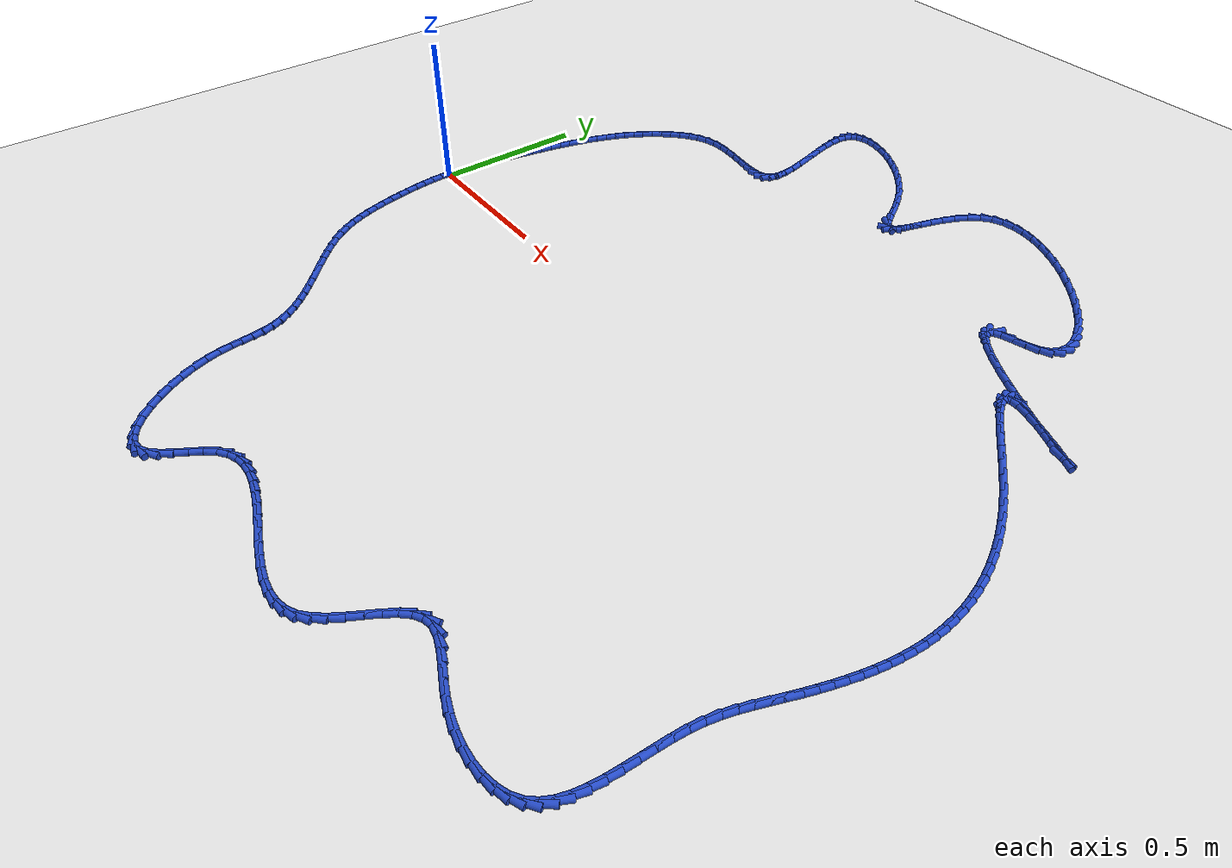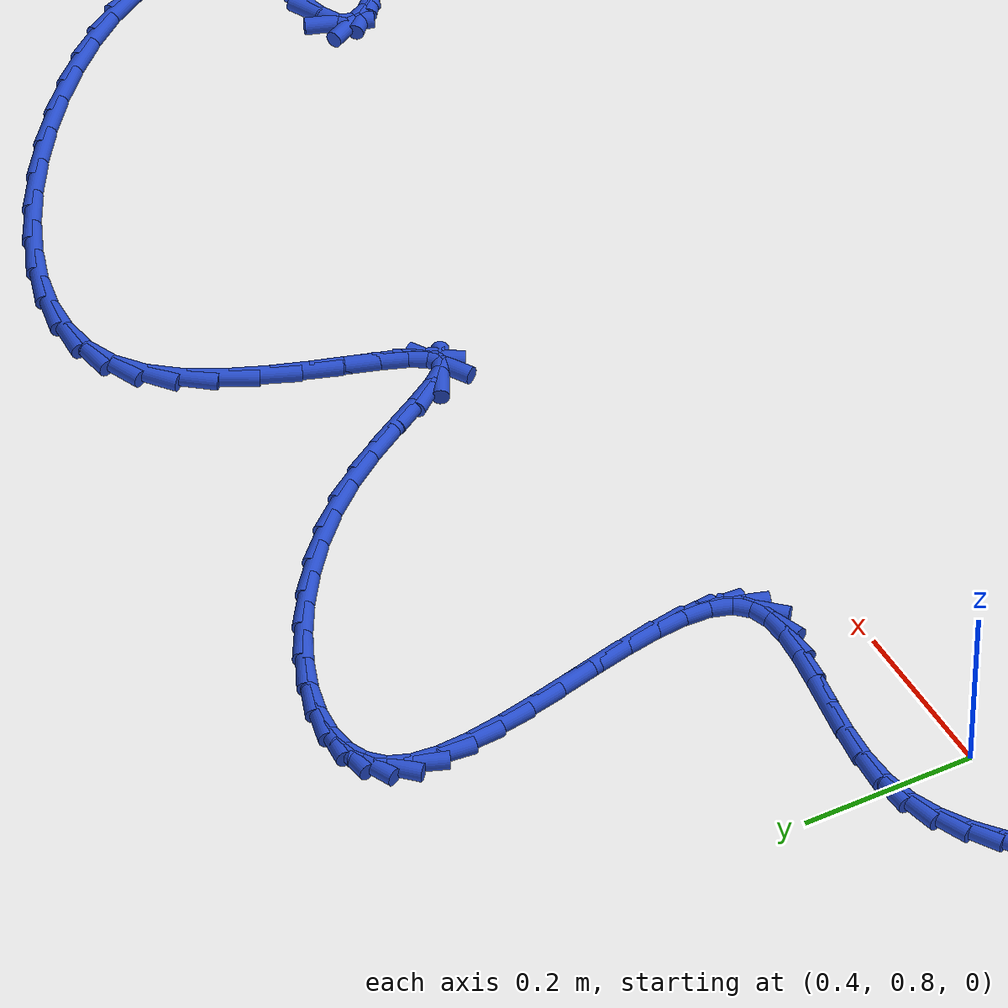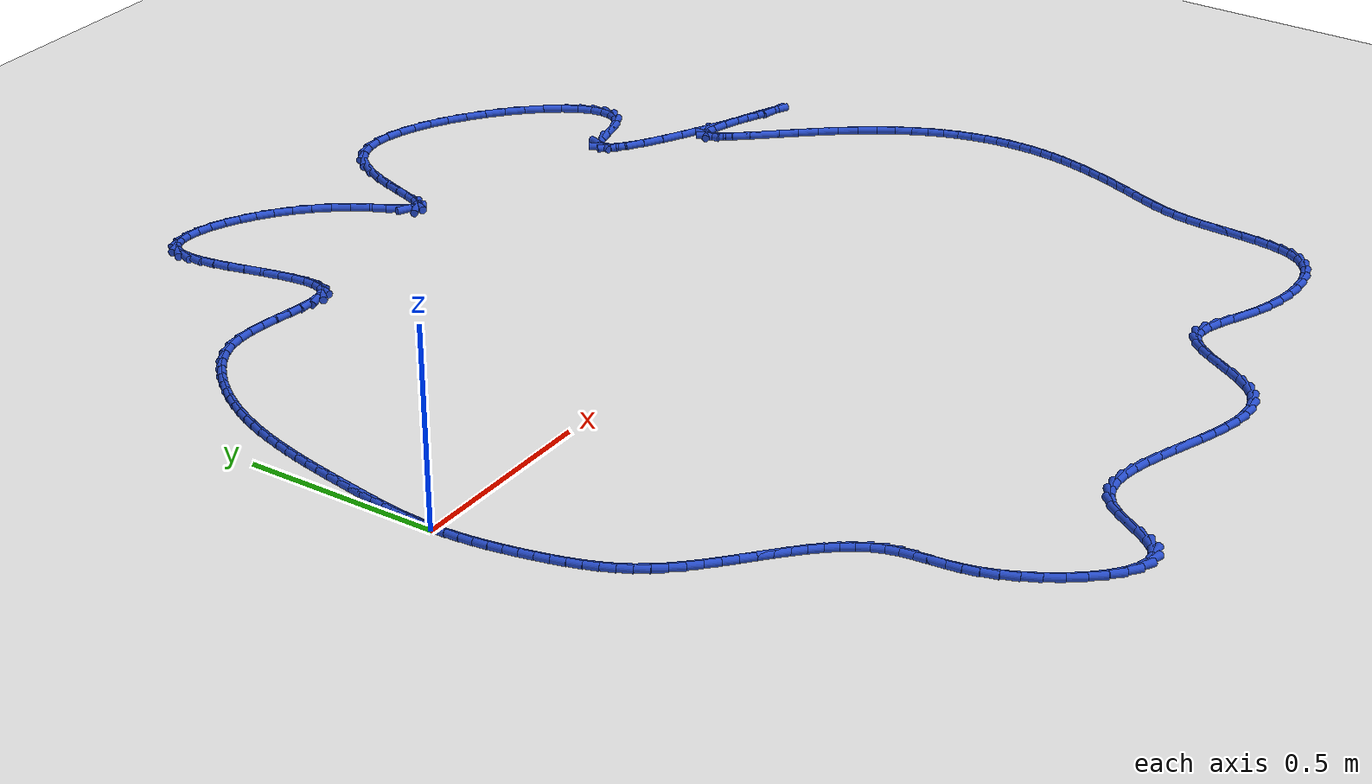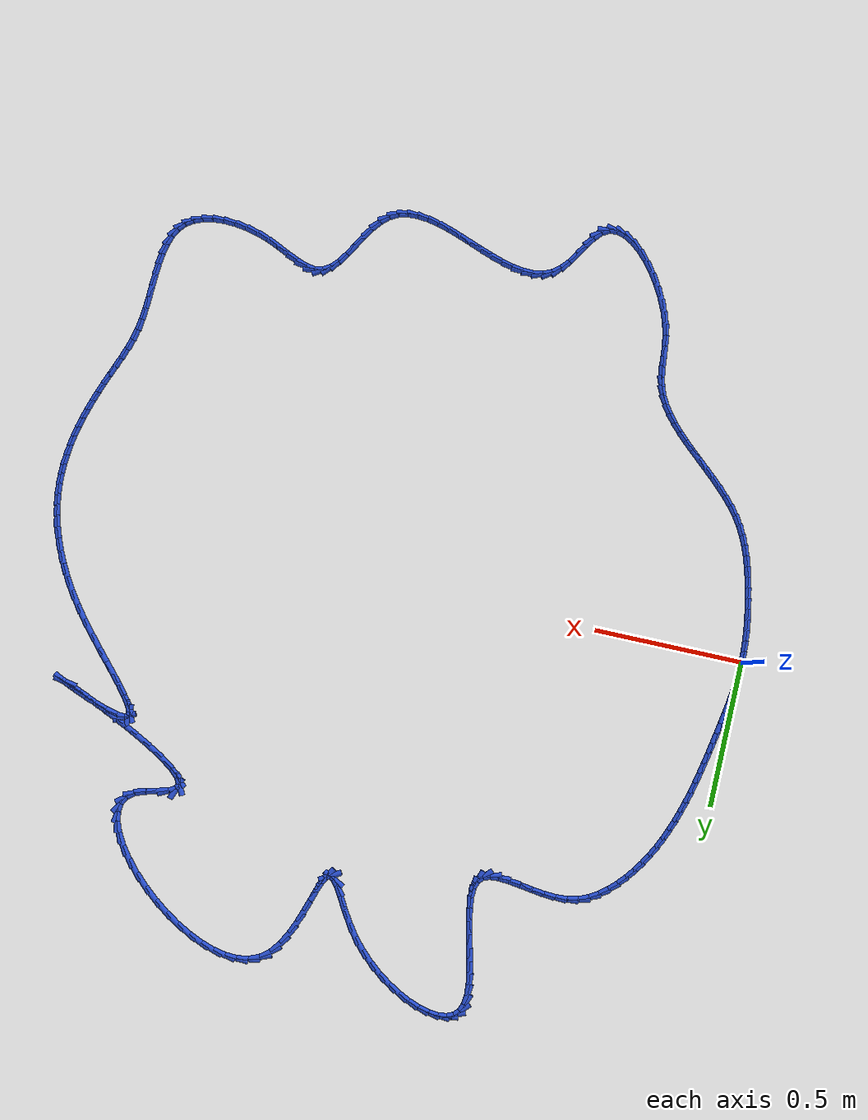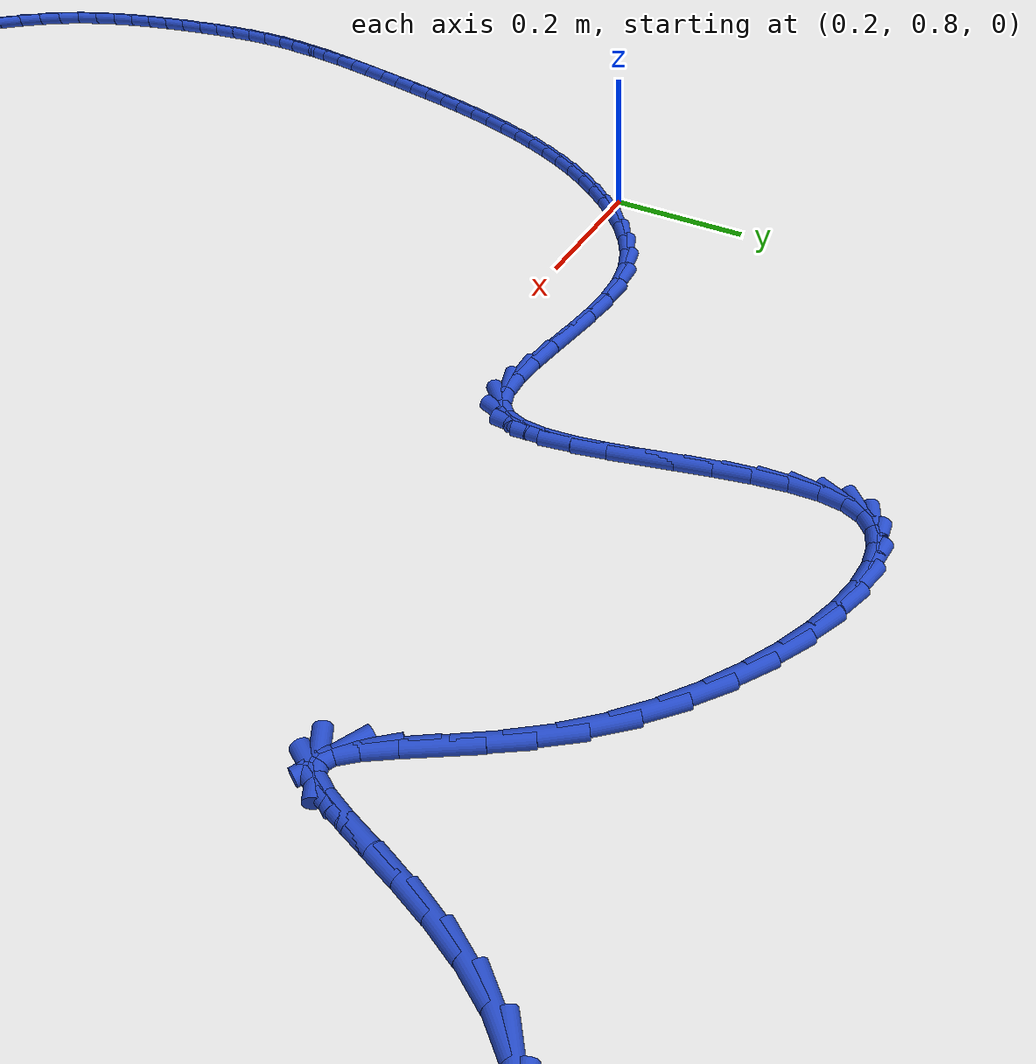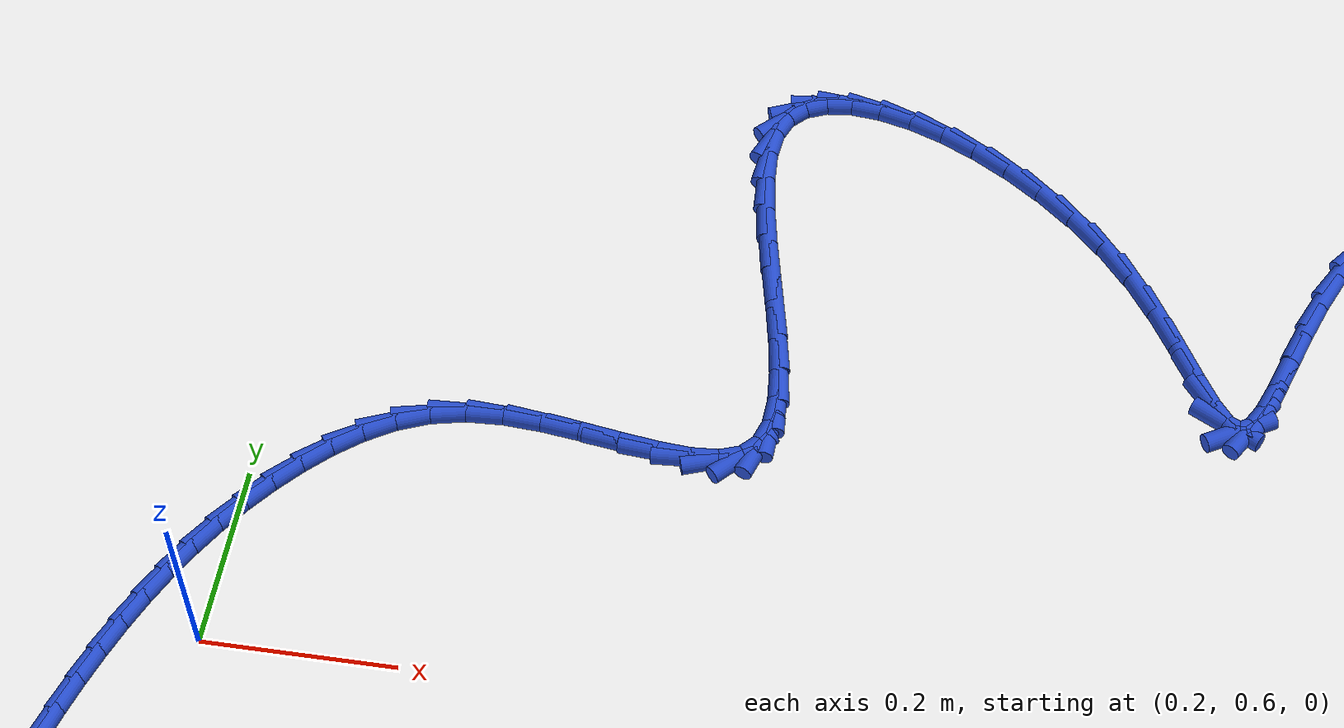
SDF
<sdf version="1.6">
 <world name="default">
  <light name="sun" type="directional">
   <pose>0 0 10 0 -0 0</pose>
   <diffuse>0.8 0.8 0.8 1</diffuse>
   <specular>0.2 0.2 0.2 1</specular>
   <attenuation>
    <range>1000</range>
    <constant>0.9</constant>
    <linear>0.01</linear>
    <quadratic>0.001</quadratic>
   </attenuation>
   <direction>-0.5 0.1 -0.9</direction>
  </light>
  <model name="ground_plane">
   <static>1</static>
   <link name="link">
    <collision name="collision">
     <geometry><plane><normal>0 0 1</normal><size>100 100</size></plane></geometry>
     <surface><friction><ode><mu>100</mu><mu2>50</mu2></ode></friction></surface>
    </collision>
    <visual name="visual">
     <cast_shadows>0</cast_shadows>
     <geometry><plane><normal>0 0 1</normal><size>100 100</size></plane></geometry>
     <material>
      <script><uri>file://media/materials/scripts/gazebo.material</uri><name>Gazebo/WhiteGlow</name></script>
     </material>
    </visual>
   </link>
  </model>
  <gravity>0 0 -9.8</gravity>
  <magnetic_field>6e-06 2.3e-05 -4.2e-05</magnetic_field>
  <atmosphere type="adiabatic"/>
  <physics name="default_physics" default="0" type="ode">
   <max_step_size>0.001</max_step_size>
   <real_time_factor>1</real_time_factor>
   <real_time_update_rate>1000</real_time_update_rate>
  </physics>
  <scene><ambient>0.4 0.4 0.4 1</ambient><background>0.7 0.7 0.7 1</background><shadows>1</shadows></scene>
  <spherical_coordinates>
   <surface_model>EARTH_WGS84</surface_model>
   <latitude_deg>0</latitude_deg>
   <longitude_deg>0</longitude_deg>
   <elevation>0</elevation>
   <heading_deg>0</heading_deg>
  </spherical_coordinates>
  <model name="line">
   <link name="link_0">
    <pose>-2.6020852139652106e-18 -2.7755575615628914e-17 0.01 0 1.57 1.538051341672518</pose>
    <collision name="collision">
     <geometry><cylinder><radius>0.01</radius><length>0.08</length></cylinder></geometry>
    </collision>
    <visual name="visual">
     <material>
      <script><name>Gazebo/Blue</name><uri>file://media/materials/scripts/gazebo.material</uri></script>
     </material>
     <geometry><cylinder><radius>0.01</radius><length>0.08</length></cylinder></geometry>
    </visual>
   </link>
   <link name="link_1">
    <pose>0.0011565233107194892 0.035306472801564744 0.01 0 1.57 1.4963231635099927</pose>
    <collision name="collision">
     <geometry><cylinder><radius>0.01</radius><length>0.08</length></cylinder></geometry>
    </collision>
    <visual name="visual">
     <material>
      <script><name>Gazebo/Blue</name><uri>file://media/materials/scripts/gazebo.material</uri></script>
     </material>
     <geometry><cylinder><radius>0.01</radius><length>0.08</length></cylinder></geometry>
    </visual>
   </link>
   <link name="link_2">
    <pose>0.0037874917238029113 0.0705688746276953 0.01 0 1.57 1.4616681048065028</pose>
    <collision name="collision">
     <geometry><cylinder><radius>0.01</radius><length>0.08</length></cylinder></geometry>
    </collision>
    <visual name="visual">
     <material>
      <script><name>Gazebo/Blue</name><uri>file://media/materials/scripts/gazebo.material</uri></script>
     </material>
     <geometry><cylinder><radius>0.01</radius><length>0.08</length></cylinder></geometry>
    </visual>
   </link>
   <link name="link_3">
    <pose>0.00765183445429029 0.10583922316953667 0.01 0 1.57 1.4341884930419941</pose>
    <collision name="collision">
     <geometry><cylinder><radius>0.01</radius><length>0.08</length></cylinder></geometry>
    </collision>
    <visual name="visual">
     <material>
      <script><name>Gazebo/Blue</name><uri>file://media/materials/scripts/gazebo.material</uri></script>
     </material>
     <geometry><cylinder><radius>0.01</radius><length>0.08</length></cylinder></geometry>
    </visual>
   </link>
   <link name="link_4">
    <pose>0.012508480717221644 0.1411695361182339 0.01 0 1.57 1.4138716343164732</pose>
    <collision name="collision">
     <geometry><cylinder><radius>0.01</radius><length>0.08</length></cylinder></geometry>
    </collision>
    <visual name="visual">
     <material>
      <script><name>Gazebo/Blue</name><uri>file://media/materials/scripts/gazebo.material</uri></script>
     </material>
     <geometry><cylinder><radius>0.01</radius><length>0.08</length></cylinder></geometry>
    </visual>
   </link>
   <link name="link_5">
    <pose>0.018116359727636994 0.17661183116493212 0.01 0 1.57 1.4006332574241642</pose>
    <collision name="collision">
     <geometry><cylinder><radius>0.01</radius><length>0.08</length></cylinder></geometry>
    </collision>
    <visual name="visual">
     <material>
      <script><name>Gazebo/Blue</name><uri>file://media/materials/scripts/gazebo.material</uri></script>
     </material>
     <geometry><cylinder><radius>0.01</radius><length>0.08</length></cylinder></geometry>
    </visual>
   </link>
   <link name="link_6">
    <pose>0.024234400700576357 0.2122181260007763 0.01 0 1.57 1.3943255280495659</pose>
    <collision name="collision">
     <geometry><cylinder><radius>0.01</radius><length>0.08</length></cylinder></geometry>
    </collision>
    <visual name="visual">
     <material>
      <script><name>Gazebo/Blue</name><uri>file://media/materials/scripts/gazebo.material</uri></script>
     </material>
     <geometry><cylinder><radius>0.01</radius><length>0.08</length></cylinder></geometry>
    </visual>
   </link>
   <link name="link_7">
    <pose>0.030622379469162415 0.24804008281447187 0.01 0 1.57 1.391630001763607</pose>
    <collision name="collision">
     <geometry><cylinder><radius>0.01</radius><length>0.08</length></cylinder></geometry>
    </collision>
    <visual name="visual">
     <material>
      <script><name>Gazebo/Blue</name><uri>file://media/materials/scripts/gazebo.material</uri></script>
     </material>
     <geometry><cylinder><radius>0.01</radius><length>0.08</length></cylinder></geometry>
    </visual>
   </link>
   <link name="link_8">
    <pose>0.03715008431257833 0.28408316859316796 0.01 0 1.57 1.38620507308836</pose>
    <collision name="collision">
     <geometry><cylinder><radius>0.01</radius><length>0.08</length></cylinder></geometry>
    </collision>
    <visual name="visual">
     <material>
      <script><name>Gazebo/Blue</name><uri>file://media/materials/scripts/gazebo.material</uri></script>
     </material>
     <geometry><cylinder><radius>0.01</radius><length>0.08</length></cylinder></geometry>
    </visual>
   </link>
   <link name="link_9">
    <pose>0.04390516262457887 0.320261369350098 0.01 0 1.57 1.377322085851428</pose>
    <collision name="collision">
     <geometry><cylinder><radius>0.01</radius><length>0.08</length></cylinder></geometry>
    </collision>
    <visual name="visual">
     <material>
      <script><name>Gazebo/Blue</name><uri>file://media/materials/scripts/gazebo.material</uri></script>
     </material>
     <geometry><cylinder><radius>0.01</radius><length>0.08</length></cylinder></geometry>
    </visual>
   </link>
   <link name="link_10">
    <pose>0.051000888513635295 0.3564779102137596 0.01 0 1.57 1.364958096829059</pose>
    <collision name="collision">
     <geometry><cylinder><radius>0.01</radius><length>0.08</length></cylinder></geometry>
    </collision>
    <visual name="visual">
     <material>
      <script><name>Gazebo/Blue</name><uri>file://media/materials/scripts/gazebo.material</uri></script>
     </material>
     <geometry><cylinder><radius>0.01</radius><length>0.08</length></cylinder></geometry>
    </visual>
   </link>
   <link name="link_11">
    <pose>0.05855053608821886 0.3926360163126499 0.01 0 1.57 1.3490538640448173</pose>
    <collision name="collision">
     <geometry><cylinder><radius>0.01</radius><length>0.08</length></cylinder></geometry>
    </collision>
    <visual name="visual">
     <material>
      <script><name>Gazebo/Blue</name><uri>file://media/materials/scripts/gazebo.material</uri></script>
     </material>
     <geometry><cylinder><radius>0.01</radius><length>0.08</length></cylinder></geometry>
    </visual>
   </link>
   <link name="link_12">
    <pose>0.06666737945680083 0.42863891277526694 0.01 0 1.57 1.3295176159188433</pose>
    <collision name="collision">
     <geometry><cylinder><radius>0.01</radius><length>0.08</length></cylinder></geometry>
    </collision>
    <visual name="visual">
     <material>
      <script><name>Gazebo/Blue</name><uri>file://media/materials/scripts/gazebo.material</uri></script>
     </material>
     <geometry><cylinder><radius>0.01</radius><length>0.08</length></cylinder></geometry>
    </visual>
   </link>
   <link name="link_13">
    <pose>0.0754646927278525 0.4643898247301082 0.01 0 1.57 1.306229672828329</pose>
    <collision name="collision">
     <geometry><cylinder><radius>0.01</radius><length>0.08</length></cylinder></geometry>
    </collision>
    <visual name="visual">
     <material>
      <script><name>Gazebo/Blue</name><uri>file://media/materials/scripts/gazebo.material</uri></script>
     </material>
     <geometry><cylinder><radius>0.01</radius><length>0.08</length></cylinder></geometry>
    </visual>
   </link>
   <link name="link_14">
    <pose>0.08505575000984508 0.499791977305671 0.01 0 1.57 1.2790485048740847</pose>
    <collision name="collision">
     <geometry><cylinder><radius>0.01</radius><length>0.08</length></cylinder></geometry>
    </collision>
    <visual name="visual">
     <material>
      <script><name>Gazebo/Blue</name><uri>file://media/materials/scripts/gazebo.material</uri></script>
     </material>
     <geometry><cylinder><radius>0.01</radius><length>0.08</length></cylinder></geometry>
    </visual>
   </link>
   <link name="link_15">
    <pose>0.0955538254112499 0.5347485956304533 0.01 0 1.57 1.2478189335547443</pose>
    <collision name="collision">
     <geometry><cylinder><radius>0.01</radius><length>0.08</length></cylinder></geometry>
    </collision>
    <visual name="visual">
     <material>
      <script><name>Gazebo/Blue</name><uri>file://media/materials/scripts/gazebo.material</uri></script>
     </material>
     <geometry><cylinder><radius>0.01</radius><length>0.08</length></cylinder></geometry>
    </visual>
   </link>
   <link name="link_16">
    <pose>0.10707219304053817 0.5691629048329523 0.01 0 1.57 1.212383278387367</pose>
    <collision name="collision">
     <geometry><cylinder><radius>0.01</radius><length>0.08</length></cylinder></geometry>
    </collision>
    <visual name="visual">
     <material>
      <script><name>Gazebo/Blue</name><uri>file://media/materials/scripts/gazebo.material</uri></script>
     </material>
     <geometry><cylinder><radius>0.01</radius><length>0.08</length></cylinder></geometry>
    </visual>
   </link>
   <link name="link_17">
    <pose>0.11972412700618121 0.6029381300416659 0.01 0 1.57 1.172596258499799</pose>
    <collision name="collision">
     <geometry><cylinder><radius>0.01</radius><length>0.08</length></cylinder></geometry>
    </collision>
    <visual name="visual">
     <material>
      <script><name>Gazebo/Blue</name><uri>file://media/materials/scripts/gazebo.material</uri></script>
     </material>
     <geometry><cylinder><radius>0.01</radius><length>0.08</length></cylinder></geometry>
    </visual>
   </link>
   <link name="link_18">
    <pose>0.13362290141665017 0.6359774963850912 0.01 0 1.57 1.128344297698051</pose>
    <collision name="collision">
     <geometry><cylinder><radius>0.01</radius><length>0.08</length></cylinder></geometry>
    </collision>
    <visual name="visual">
     <material>
      <script><name>Gazebo/Blue</name><uri>file://media/materials/scripts/gazebo.material</uri></script>
     </material>
     <geometry><cylinder><radius>0.01</radius><length>0.08</length></cylinder></geometry>
    </visual>
   </link>
   <link name="link_19">
    <pose>0.1488817903804165 0.6681842289917264 0.01 0 1.57 1.0795694333273218</pose>
    <collision name="collision">
     <geometry><cylinder><radius>0.01</radius><length>0.08</length></cylinder></geometry>
    </collision>
    <visual name="visual">
     <material>
      <script><name>Gazebo/Blue</name><uri>file://media/materials/scripts/gazebo.material</uri></script>
     </material>
     <geometry><cylinder><radius>0.01</radius><length>0.08</length></cylinder></geometry>
    </visual>
   </link>
   <link name="link_20">
    <pose>0.1656140680059513 0.6994615529900685 0.01 0 1.57 1.0262971724834187</pose>
    <collision name="collision">
     <geometry><cylinder><radius>0.01</radius><length>0.08</length></cylinder></geometry>
    </collision>
    <visual name="visual">
     <material>
      <script><name>Gazebo/Blue</name><uri>file://media/materials/scripts/gazebo.material</uri></script>
     </material>
     <geometry><cylinder><radius>0.01</radius><length>0.08</length></cylinder></geometry>
    </visual>
   </link>
   <link name="link_21">
    <pose>0.1839330084017259 0.7297126935086153 0.01 0 1.57 0.968666308309646</pose>
    <collision name="collision">
     <geometry><cylinder><radius>0.01</radius><length>0.08</length></cylinder></geometry>
    </collision>
    <visual name="visual">
     <material>
      <script><name>Gazebo/Blue</name><uri>file://media/materials/scripts/gazebo.material</uri></script>
     </material>
     <geometry><cylinder><radius>0.01</radius><length>0.08</length></cylinder></geometry>
    </visual>
   </link>
   <link name="link_22">
    <pose>0.20395188567621161 0.7588408756758646 0.01 0 1.57 0.9069570021050652</pose>
    <collision name="collision">
     <geometry><cylinder><radius>0.01</radius><length>0.08</length></cylinder></geometry>
    </collision>
    <visual name="visual">
     <material>
      <script><name>Gazebo/Blue</name><uri>file://media/materials/scripts/gazebo.material</uri></script>
     </material>
     <geometry><cylinder><radius>0.01</radius><length>0.08</length></cylinder></geometry>
    </visual>
   </link>
   <link name="link_23">
    <pose>0.22578397393787963 0.7867493246203134 0.01 0 1.57 0.8416078980378938</pose>
    <collision name="collision">
     <geometry><cylinder><radius>0.01</radius><length>0.08</length></cylinder></geometry>
    </collision>
    <visual name="visual">
     <material>
      <script><name>Gazebo/Blue</name><uri>file://media/materials/scripts/gazebo.material</uri></script>
     </material>
     <geometry><cylinder><radius>0.01</radius><length>0.08</length></cylinder></geometry>
    </visual>
   </link>
   <link name="link_24">
    <pose>0.24954257643883898 0.8133410925379823 0.01 0 1.57 0.7681548256375087</pose>
    <collision name="collision">
     <geometry><cylinder><radius>0.01</radius><length>0.08</length></cylinder></geometry>
    </collision>
    <visual name="visual">
     <material>
      <script><name>Gazebo/Blue</name><uri>file://media/materials/scripts/gazebo.material</uri></script>
     </material>
     <geometry><cylinder><radius>0.01</radius><length>0.08</length></cylinder></geometry>
    </visual>
   </link>
   <link name="link_25">
    <pose>0.27537787014443277 0.8383004304359555 0.01 0 1.57 0.6709944471113306</pose>
    <collision name="collision">
     <geometry><cylinder><radius>0.01</radius><length>0.08</length></cylinder></geometry>
    </collision>
    <visual name="visual">
     <material>
      <script><name>Gazebo/Blue</name><uri>file://media/materials/scripts/gazebo.material</uri></script>
     </material>
     <geometry><cylinder><radius>0.01</radius><length>0.08</length></cylinder></geometry>
    </visual>
   </link>
   <link name="link_26">
    <pose>0.30354903493636803 0.8606647879659345 0.01 0 1.57 0.5455654605953032</pose>
    <collision name="collision">
     <geometry><cylinder><radius>0.01</radius><length>0.08</length></cylinder></geometry>
    </collision>
    <visual name="visual">
     <material>
      <script><name>Gazebo/Blue</name><uri>file://media/materials/scripts/gazebo.material</uri></script>
     </material>
     <geometry><cylinder><radius>0.01</radius><length>0.08</length></cylinder></geometry>
    </visual>
   </link>
   <link name="link_27">
    <pose>0.3343352957446367 0.8793526714996421 0.01 0 1.57 0.39216581043727256</pose>
    <collision name="collision">
     <geometry><cylinder><radius>0.01</radius><length>0.08</length></cylinder></geometry>
    </collision>
    <visual name="visual">
     <material>
      <script><name>Gazebo/Blue</name><uri>file://media/materials/scripts/gazebo.material</uri></script>
     </material>
     <geometry><cylinder><radius>0.01</radius><length>0.08</length></cylinder></geometry>
    </visual>
   </link>
   <link name="link_28">
    <pose>0.3680158774992311 0.8932825874088011 0.01 0 1.57 0.21618795078555159</pose>
    <collision name="collision">
     <geometry><cylinder><radius>0.01</radius><length>0.08</length></cylinder></geometry>
    </collision>
    <visual name="visual">
     <material>
      <script><name>Gazebo/Blue</name><uri>file://media/materials/scripts/gazebo.material</uri></script>
     </material>
     <geometry><cylinder><radius>0.01</radius><length>0.08</length></cylinder></geometry>
    </visual>
   </link>
   <link name="link_29">
    <pose>0.4048682491638367 0.9013761103642667 0.01 0 1.57 0.049440580541957505</pose>
    <collision name="collision">
     <geometry><cylinder><radius>0.01</radius><length>0.08</length></cylinder></geometry>
    </collision>
    <visual name="visual">
     <material>
      <script><name>Gazebo/Blue</name><uri>file://media/materials/scripts/gazebo.material</uri></script>
     </material>
     <geometry><cylinder><radius>0.01</radius><length>0.08</length></cylinder></geometry>
    </visual>
   </link>
   <link name="link_30">
    <pose>0.44471605097719286 0.9033478156074725 0.01 0 1.57 -0.06217576872446289</pose>
    <collision name="collision">
     <geometry><cylinder><radius>0.01</radius><length>0.08</length></cylinder></geometry>
    </collision>
    <visual name="visual">
     <material>
      <script><name>Gazebo/Blue</name><uri>file://media/materials/scripts/gazebo.material</uri></script>
     </material>
     <geometry><cylinder><radius>0.01</radius><length>0.08</length></cylinder></geometry>
    </visual>
   </link>
   <link name="link_31">
    <pose>0.48632704081781813 0.9007572812809346 0.01 0 1.57 -0.12628590295770223</pose>
    <collision name="collision">
     <geometry><cylinder><radius>0.01</radius><length>0.08</length></cylinder></geometry>
    </collision>
    <visual name="visual">
     <material>
      <script><name>Gazebo/Blue</name><uri>file://media/materials/scripts/gazebo.material</uri></script>
     </material>
     <geometry><cylinder><radius>0.01</radius><length>0.08</length></cylinder></geometry>
    </visual>
   </link>
   <link name="link_32">
    <pose>0.5283191426777786 0.8954258987419723 0.01 0 1.57 -0.1513266641243258</pose>
    <collision name="collision">
     <geometry><cylinder><radius>0.01</radius><length>0.08</length></cylinder></geometry>
    </collision>
    <visual name="visual">
     <material>
      <script><name>Gazebo/Blue</name><uri>file://media/materials/scripts/gazebo.material</uri></script>
     </material>
     <geometry><cylinder><radius>0.01</radius><length>0.08</length></cylinder></geometry>
    </visual>
   </link>
   <link name="link_33">
    <pose>0.5693102805491403 0.8891750593479059 0.01 0 1.57 -0.13766725404210428</pose>
    <collision name="collision">
     <geometry><cylinder><radius>0.01</radius><length>0.08</length></cylinder></geometry>
    </collision>
    <visual name="visual">
     <material>
      <script><name>Gazebo/Blue</name><uri>file://media/materials/scripts/gazebo.material</uri></script>
     </material>
     <geometry><cylinder><radius>0.01</radius><length>0.08</length></cylinder></geometry>
    </visual>
   </link>
   <link name="link_34">
    <pose>0.60791837842397 0.8838261544560547 0.01 0 1.57 -0.07521245691974714</pose>
    <collision name="collision">
     <geometry><cylinder><radius>0.01</radius><length>0.08</length></cylinder></geometry>
    </collision>
    <visual name="visual">
     <material>
      <script><name>Gazebo/Blue</name><uri>file://media/materials/scripts/gazebo.material</uri></script>
     </material>
     <geometry><cylinder><radius>0.01</radius><length>0.08</length></cylinder></geometry>
    </visual>
   </link>
   <link name="link_35">
    <pose>0.6427613602943336 0.8812005754237386 0.01 0 1.57 0.0645368601420958</pose>
    <collision name="collision">
     <geometry><cylinder><radius>0.01</radius><length>0.08</length></cylinder></geometry>
    </collision>
    <visual name="visual">
     <material>
      <script><name>Gazebo/Blue</name><uri>file://media/materials/scripts/gazebo.material</uri></script>
     </material>
     <geometry><cylinder><radius>0.01</radius><length>0.08</length></cylinder></geometry>
    </visual>
   </link>
   <link name="link_36">
    <pose>0.6724571501522971 0.8831197136082769 0.01 0 1.57 0.3434637001141684</pose>
    <collision name="collision">
     <geometry><cylinder><radius>0.01</radius><length>0.08</length></cylinder></geometry>
    </collision>
    <visual name="visual">
     <material>
      <script><name>Gazebo/Blue</name><uri>file://media/materials/scripts/gazebo.material</uri></script>
     </material>
     <geometry><cylinder><radius>0.01</radius><length>0.08</length></cylinder></geometry>
    </visual>
   </link>
   <link name="link_37">
    <pose>0.6956236719899268 0.8914049603669897 0.01 0 1.57 0.81470989247443</pose>
    <collision name="collision">
     <geometry><cylinder><radius>0.01</radius><length>0.08</length></cylinder></geometry>
    </collision>
    <visual name="visual">
     <material>
      <script><name>Gazebo/Blue</name><uri>file://media/materials/scripts/gazebo.material</uri></script>
     </material>
     <geometry><cylinder><radius>0.01</radius><length>0.08</length></cylinder></geometry>
    </visual>
   </link>
   <link name="link_38">
    <pose>0.7110110093431282 0.9077218702640225 0.01 0 1.57 1.2558039798307685</pose>
    <collision name="collision">
     <geometry><cylinder><radius>0.01</radius><length>0.08</length></cylinder></geometry>
    </collision>
    <visual name="visual">
     <material>
      <script><name>Gazebo/Blue</name><uri>file://media/materials/scripts/gazebo.material</uri></script>
     </material>
     <geometry><cylinder><radius>0.01</radius><length>0.08</length></cylinder></geometry>
    </visual>
   </link>
   <link name="link_39">
    <pose>0.7188995199551486 0.9319315649922969 0.01 0 1.57 1.5171374051745228</pose>
    <collision name="collision">
     <geometry><cylinder><radius>0.01</radius><length>0.08</length></cylinder></geometry>
    </collision>
    <visual name="visual">
     <material>
      <script><name>Gazebo/Blue</name><uri>file://media/materials/scripts/gazebo.material</uri></script>
     </material>
     <geometry><cylinder><radius>0.01</radius><length>0.08</length></cylinder></geometry>
    </visual>
   </link>
   <link name="link_40">
    <pose>0.7205539556480465 0.9627344115084111 0.01 0 1.57 -1.4796177917465425</pose>
    <collision name="collision">
     <geometry><cylinder><radius>0.01</radius><length>0.08</length></cylinder></geometry>
    </collision>
    <visual name="visual">
     <material>
      <script><name>Gazebo/Blue</name><uri>file://media/materials/scripts/gazebo.material</uri></script>
     </material>
     <geometry><cylinder><radius>0.01</radius><length>0.08</length></cylinder></geometry>
    </visual>
   </link>
   <link name="link_41">
    <pose>0.7172553459221657 0.9988115828378208 0.01 0 1.57 -1.3984013100552064</pose>
    <collision name="collision">
     <geometry><cylinder><radius>0.01</radius><length>0.08</length></cylinder></geometry>
    </collision>
    <visual name="visual">
     <material>
      <script><name>Gazebo/Blue</name><uri>file://media/materials/scripts/gazebo.material</uri></script>
     </material>
     <geometry><cylinder><radius>0.01</radius><length>0.08</length></cylinder></geometry>
    </visual>
   </link>
   <link name="link_42">
    <pose>0.7102847202778497 1.0388442520059826 0.01 0 1.57 -1.354819314364594</pose>
    <collision name="collision">
     <geometry><cylinder><radius>0.01</radius><length>0.08</length></cylinder></geometry>
    </collision>
    <visual name="visual">
     <material>
      <script><name>Gazebo/Blue</name><uri>file://media/materials/scripts/gazebo.material</uri></script>
     </material>
     <geometry><cylinder><radius>0.01</radius><length>0.08</length></cylinder></geometry>
    </visual>
   </link>
   <link name="link_43">
    <pose>0.7009231082154428 1.081513592038351 0.01 0 1.57 -1.3370869246457529</pose>
    <collision name="collision">
     <geometry><cylinder><radius>0.01</radius><length>0.08</length></cylinder></geometry>
    </collision>
    <visual name="visual">
     <material>
      <script><name>Gazebo/Blue</name><uri>file://media/materials/scripts/gazebo.material</uri></script>
     </material>
     <geometry><cylinder><radius>0.01</radius><length>0.08</length></cylinder></geometry>
    </visual>
   </link>
   <link name="link_44">
    <pose>0.6904515392352885 1.125500775960382 0.01 0 1.57 -1.3407657341686434</pose>
    <collision name="collision">
     <geometry><cylinder><radius>0.01</radius><length>0.08</length></cylinder></geometry>
    </collision>
    <visual name="visual">
     <material>
      <script><name>Gazebo/Blue</name><uri>file://media/materials/scripts/gazebo.material</uri></script>
     </material>
     <geometry><cylinder><radius>0.01</radius><length>0.08</length></cylinder></geometry>
    </visual>
   </link>
   <link name="link_45">
    <pose>0.680151042837731 1.169486976797531 0.01 0 1.57 -1.3663094359716972</pose>
    <collision name="collision">
     <geometry><cylinder><radius>0.01</radius><length>0.08</length></cylinder></geometry>
    </collision>
    <visual name="visual">
     <material>
      <script><name>Gazebo/Blue</name><uri>file://media/materials/scripts/gazebo.material</uri></script>
     </material>
     <geometry><cylinder><radius>0.01</radius><length>0.08</length></cylinder></geometry>
    </visual>
   </link>
   <link name="link_46">
    <pose>0.6713026485231137 1.2121533675752552 0.01 0 1.57 -1.4191930007503297</pose>
    <collision name="collision">
     <geometry><cylinder><radius>0.01</radius><length>0.08</length></cylinder></geometry>
    </collision>
    <visual name="visual">
     <material>
      <script><name>Gazebo/Blue</name><uri>file://media/materials/scripts/gazebo.material</uri></script>
     </material>
     <geometry><cylinder><radius>0.01</radius><length>0.08</length></cylinder></geometry>
    </visual>
   </link>
   <link name="link_47">
    <pose>0.6651873857917808 1.2521811213190082 0.01 0 1.57 -1.5126118740710122</pose>
    <collision name="collision">
     <geometry><cylinder><radius>0.01</radius><length>0.08</length></cylinder></geometry>
    </collision>
    <visual name="visual">
     <material>
      <script><name>Gazebo/Blue</name><uri>file://media/materials/scripts/gazebo.material</uri></script>
     </material>
     <geometry><cylinder><radius>0.01</radius><length>0.08</length></cylinder></geometry>
    </visual>
   </link>
   <link name="link_48">
    <pose>0.6630862841440766 1.2882514110542471 0.01 0 1.57 1.4674415289961418</pose>
    <collision name="collision">
     <geometry><cylinder><radius>0.01</radius><length>0.08</length></cylinder></geometry>
    </collision>
    <visual name="visual">
     <material>
      <script><name>Gazebo/Blue</name><uri>file://media/materials/scripts/gazebo.material</uri></script>
     </material>
     <geometry><cylinder><radius>0.01</radius><length>0.08</length></cylinder></geometry>
    </visual>
   </link>
   <link name="link_49">
    <pose>0.666280373080344 1.3190454098064266 0.01 0 1.57 1.187357471151704</pose>
    <collision name="collision">
     <geometry><cylinder><radius>0.01</radius><length>0.08</length></cylinder></geometry>
    </collision>
    <visual name="visual">
     <material>
      <script><name>Gazebo/Blue</name><uri>file://media/materials/scripts/gazebo.material</uri></script>
     </material>
     <geometry><cylinder><radius>0.01</radius><length>0.08</length></cylinder></geometry>
    </visual>
   </link>
   <link name="link_50">
    <pose>0.6760443005650691 1.3432491530264072 0.01 0 1.57 0.7843848226677435</pose>
    <collision name="collision">
     <geometry><cylinder><radius>0.01</radius><length>0.08</length></cylinder></geometry>
    </collision>
    <visual name="visual">
     <material>
      <script><name>Gazebo/Blue</name><uri>file://media/materials/scripts/gazebo.material</uri></script>
     </material>
     <geometry><cylinder><radius>0.01</radius><length>0.08</length></cylinder></geometry>
    </visual>
   </link>
   <link name="link_51">
    <pose>0.6929292527932961 1.3600999194651617 0.01 0 1.57 0.3995222672710092</pose>
    <collision name="collision">
     <geometry><cylinder><radius>0.01</radius><length>0.08</length></cylinder></geometry>
    </collision>
    <visual name="visual">
     <material>
      <script><name>Gazebo/Blue</name><uri>file://media/materials/scripts/gazebo.material</uri></script>
     </material>
     <geometry><cylinder><radius>0.01</radius><length>0.08</length></cylinder></geometry>
    </visual>
   </link>
   <link name="link_52">
    <pose>0.7161068079275333 1.369886183274504 0.01 0 1.57 0.10937940458509372</pose>
    <collision name="collision">
     <geometry><cylinder><radius>0.01</radius><length>0.08</length></cylinder></geometry>
    </collision>
    <visual name="visual">
     <material>
      <script><name>Gazebo/Blue</name><uri>file://media/materials/scripts/gazebo.material</uri></script>
     </material>
     <geometry><cylinder><radius>0.01</radius><length>0.08</length></cylinder></geometry>
    </visual>
   </link>
   <link name="link_53">
    <pose>0.7445935326822612 1.3730145299229408 0.01 0 1.57 -0.09489096164080808</pose>
    <collision name="collision">
     <geometry><cylinder><radius>0.01</radius><length>0.08</length></cylinder></geometry>
    </collision>
    <visual name="visual">
     <material>
      <script><name>Gazebo/Blue</name><uri>file://media/materials/scripts/gazebo.material</uri></script>
     </material>
     <geometry><cylinder><radius>0.01</radius><length>0.08</length></cylinder></geometry>
    </visual>
   </link>
   <link name="link_54">
    <pose>0.7774059937719618 1.3698915448789786 0.01 0 1.57 -0.24313059566858217</pose>
    <collision name="collision">
     <geometry><cylinder><radius>0.01</radius><length>0.08</length></cylinder></geometry>
    </collision>
    <visual name="visual">
     <material>
      <script><name>Gazebo/Blue</name><uri>file://media/materials/scripts/gazebo.material</uri></script>
     </material>
     <geometry><cylinder><radius>0.01</radius><length>0.08</length></cylinder></geometry>
    </visual>
   </link>
   <link name="link_55">
    <pose>0.8135607579111153 1.3609238136111246 0.01 0 1.57 -0.35793451003754917</pose>
    <collision name="collision">
     <geometry><cylinder><radius>0.01</radius><length>0.08</length></cylinder></geometry>
    </collision>
    <visual name="visual">
     <material>
      <script><name>Gazebo/Blue</name><uri>file://media/materials/scripts/gazebo.material</uri></script>
     </material>
     <geometry><cylinder><radius>0.01</radius><length>0.08</length></cylinder></geometry>
    </visual>
   </link>
   <link name="link_56">
    <pose>0.8520743918142022 1.3465179215878855 0.01 0 1.57 -0.45342643045555214</pose>
    <collision name="collision">
     <geometry><cylinder><radius>0.01</radius><length>0.08</length></cylinder></geometry>
    </collision>
    <visual name="visual">
     <material>
      <script><name>Gazebo/Blue</name><uri>file://media/materials/scripts/gazebo.material</uri></script>
     </material>
     <geometry><cylinder><radius>0.01</radius><length>0.08</length></cylinder></geometry>
    </visual>
   </link>
   <link name="link_57">
    <pose>0.891963462195704 1.327080454277768 0.01 0 1.57 -0.5384788990115779</pose>
    <collision name="collision">
     <geometry><cylinder><radius>0.01</radius><length>0.08</length></cylinder></geometry>
    </collision>
    <visual name="visual">
     <material>
      <script><name>Gazebo/Blue</name><uri>file://media/materials/scripts/gazebo.material</uri></script>
     </material>
     <geometry><cylinder><radius>0.01</radius><length>0.08</length></cylinder></geometry>
    </visual>
   </link>
   <link name="link_58">
    <pose>0.9322445357701018 1.3030179971492788 0.01 0 1.57 -0.6190993183804687</pose>
    <collision name="collision">
     <geometry><cylinder><radius>0.01</radius><length>0.08</length></cylinder></geometry>
    </collision>
    <visual name="visual">
     <material>
      <script><name>Gazebo/Blue</name><uri>file://media/materials/scripts/gazebo.material</uri></script>
     </material>
     <geometry><cylinder><radius>0.01</radius><length>0.08</length></cylinder></geometry>
    </visual>
   </link>
   <link name="link_59">
    <pose>0.9719341792518761 1.2747371356709247 0.01 0 1.57 -0.6998318233921846</pose>
    <collision name="collision">
     <geometry><cylinder><radius>0.01</radius><length>0.08</length></cylinder></geometry>
    </collision>
    <visual name="visual">
     <material>
      <script><name>Gazebo/Blue</name><uri>file://media/materials/scripts/gazebo.material</uri></script>
     </material>
     <geometry><cylinder><radius>0.01</radius><length>0.08</length></cylinder></geometry>
    </visual>
   </link>
   <link name="link_60">
    <pose>1.0100489593555078 1.242644455311213 0.01 0 1.57 -0.7845738702299561</pose>
    <collision name="collision">
     <geometry><cylinder><radius>0.01</radius><length>0.08</length></cylinder></geometry>
    </collision>
    <visual name="visual">
     <material>
      <script><name>Gazebo/Blue</name><uri>file://media/materials/scripts/gazebo.material</uri></script>
     </material>
     <geometry><cylinder><radius>0.01</radius><length>0.08</length></cylinder></geometry>
    </visual>
   </link>
   <link name="link_61">
    <pose>1.0456054427954782 1.2071465415386504 0.01 0 1.57 -0.8770075722311672</pose>
    <collision name="collision">
     <geometry><cylinder><radius>0.01</radius><length>0.08</length></cylinder></geometry>
    </collision>
    <visual name="visual">
     <material>
      <script><name>Gazebo/Blue</name><uri>file://media/materials/scripts/gazebo.material</uri></script>
     </material>
     <geometry><cylinder><radius>0.01</radius><length>0.08</length></cylinder></geometry>
    </visual>
   </link>
   <link name="link_62">
    <pose>1.0776217581828909 1.1686527019873008 0.01 0 1.57 -0.9664603143132241</pose>
    <collision name="collision">
     <geometry><cylinder><radius>0.01</radius><length>0.08</length></cylinder></geometry>
    </collision>
    <visual name="visual">
     <material>
      <script><name>Gazebo/Blue</name><uri>file://media/materials/scripts/gazebo.material</uri></script>
     </material>
     <geometry><cylinder><radius>0.01</radius><length>0.08</length></cylinder></geometry>
    </visual>
   </link>
   <link name="link_63">
    <pose>1.105512067776345 1.128262475090828 0.01 0 1.57 -1.024014719475255</pose>
    <collision name="collision">
     <geometry><cylinder><radius>0.01</radius><length>0.08</length></cylinder></geometry>
    </collision>
    <visual name="visual">
     <material>
      <script><name>Gazebo/Blue</name><uri>file://media/materials/scripts/gazebo.material</uri></script>
     </material>
     <geometry><cylinder><radius>0.01</radius><length>0.08</length></cylinder></geometry>
    </visual>
   </link>
   <link name="link_64">
    <pose>1.1296083669962955 1.0886750530527536 0.01 0 1.57 -1.045932911435459</pose>
    <collision name="collision">
     <geometry><cylinder><radius>0.01</radius><length>0.08</length></cylinder></geometry>
    </collision>
    <visual name="visual">
     <material>
      <script><name>Gazebo/Blue</name><uri>file://media/materials/scripts/gazebo.material</uri></script>
     </material>
     <geometry><cylinder><radius>0.01</radius><length>0.08</length></cylinder></geometry>
    </visual>
   </link>
   <link name="link_65">
    <pose>1.1503723243960713 1.0528156300609144 0.01 0 1.57 -1.0211250644223673</pose>
    <collision name="collision">
     <geometry><cylinder><radius>0.01</radius><length>0.08</length></cylinder></geometry>
    </collision>
    <visual name="visual">
     <material>
      <script><name>Gazebo/Blue</name><uri>file://media/materials/scripts/gazebo.material</uri></script>
     </material>
     <geometry><cylinder><radius>0.01</radius><length>0.08</length></cylinder></geometry>
    </visual>
   </link>
   <link name="link_66">
    <pose>1.168265608529001 1.0236094003031477 0.01 0 1.57 -0.9028643575545194</pose>
    <collision name="collision">
     <geometry><cylinder><radius>0.01</radius><length>0.08</length></cylinder></geometry>
    </collision>
    <visual name="visual">
     <material>
      <script><name>Gazebo/Blue</name><uri>file://media/materials/scripts/gazebo.material</uri></script>
     </material>
     <geometry><cylinder><radius>0.01</radius><length>0.08</length></cylinder></geometry>
    </visual>
   </link>
   <link name="link_67">
    <pose>1.1837498879484143 1.0039815579672908 0.01 0 1.57 -0.484472868882798</pose>
    <collision name="collision">
     <geometry><cylinder><radius>0.01</radius><length>0.08</length></cylinder></geometry>
    </collision>
    <visual name="visual">
     <material>
      <script><name>Gazebo/Blue</name><uri>file://media/materials/scripts/gazebo.material</uri></script>
     </material>
     <geometry><cylinder><radius>0.01</radius><length>0.08</length></cylinder></geometry>
    </visual>
   </link>
   <link name="link_68">
    <pose>1.1972868475526068 0.9968569298598281 0.01 0 1.57 0.5342681660996825</pose>
    <collision name="collision">
     <geometry><cylinder><radius>0.01</radius><length>0.08</length></cylinder></geometry>
    </collision>
    <visual name="visual">
     <material>
      <script><name>Gazebo/Blue</name><uri>file://media/materials/scripts/gazebo.material</uri></script>
     </material>
     <geometry><cylinder><radius>0.01</radius><length>0.08</length></cylinder></geometry>
    </visual>
   </link>
   <link name="link_69">
    <pose>1.2093890239799368 1.004017362185283 0.01 0 1.57 1.0451787040862872</pose>
    <collision name="collision">
     <geometry><cylinder><radius>0.01</radius><length>0.08</length></cylinder></geometry>
    </collision>
    <visual name="visual">
     <material>
      <script><name>Gazebo/Blue</name><uri>file://media/materials/scripts/gazebo.material</uri></script>
     </material>
     <geometry><cylinder><radius>0.01</radius><length>0.08</length></cylinder></geometry>
    </visual>
   </link>
   <link name="link_70">
    <pose>1.2207323001947696 1.0235732106189932 0.01 0 1.57 1.2032125602434733</pose>
    <collision name="collision">
     <geometry><cylinder><radius>0.01</radius><length>0.08</length></cylinder></geometry>
    </collision>
    <visual name="visual">
     <material>
      <script><name>Gazebo/Blue</name><uri>file://media/materials/scripts/gazebo.material</uri></script>
     </material>
     <geometry><cylinder><radius>0.01</radius><length>0.08</length></cylinder></geometry>
    </visual>
   </link>
   <link name="link_71">
    <pose>1.2320252920055705 1.052899103684971 0.01 0 1.57 1.2541263254512238</pose>
    <collision name="collision">
     <geometry><cylinder><radius>0.01</radius><length>0.08</length></cylinder></geometry>
    </collision>
    <visual name="visual">
     <material>
      <script><name>Gazebo/Blue</name><uri>file://media/materials/scripts/gazebo.material</uri></script>
     </material>
     <geometry><cylinder><radius>0.01</radius><length>0.08</length></cylinder></geometry>
    </visual>
   </link>
   <link name="link_72">
    <pose>1.2439766152208074 1.089369669907232 0.01 0 1.57 1.2566402610879577</pose>
    <collision name="collision">
     <geometry><cylinder><radius>0.01</radius><length>0.08</length></cylinder></geometry>
    </collision>
    <visual name="visual">
     <material>
      <script><name>Gazebo/Blue</name><uri>file://media/materials/scripts/gazebo.material</uri></script>
     </material>
     <geometry><cylinder><radius>0.01</radius><length>0.08</length></cylinder></geometry>
    </visual>
   </link>
   <link name="link_73">
    <pose>1.2572948856489456 1.130359537809789 0.01 0 1.57 1.2261562511648025</pose>
    <collision name="collision">
     <geometry><cylinder><radius>0.01</radius><length>0.08</length></cylinder></geometry>
    </collision>
    <visual name="visual">
     <material>
      <script><name>Gazebo/Blue</name><uri>file://media/materials/scripts/gazebo.material</uri></script>
     </material>
     <geometry><cylinder><radius>0.01</radius><length>0.08</length></cylinder></geometry>
    </visual>
   </link>
   <link name="link_74">
    <pose>1.2726887190984517 1.1732433359166565 0.01 0 1.57 1.163647638612121</pose>
    <collision name="collision">
     <geometry><cylinder><radius>0.01</radius><length>0.08</length></cylinder></geometry>
    </collision>
    <visual name="visual">
     <material>
      <script><name>Gazebo/Blue</name><uri>file://media/materials/scripts/gazebo.material</uri></script>
     </material>
     <geometry><cylinder><radius>0.01</radius><length>0.08</length></cylinder></geometry>
    </visual>
   </link>
   <link name="link_75">
    <pose>1.2908667313777928 1.2153956927518497 0.01 0 1.57 1.0613819586566187</pose>
    <collision name="collision">
     <geometry><cylinder><radius>0.01</radius><length>0.08</length></cylinder></geometry>
    </collision>
    <visual name="visual">
     <material>
      <script><name>Gazebo/Blue</name><uri>file://media/materials/scripts/gazebo.material</uri></script>
     </material>
     <geometry><cylinder><radius>0.01</radius><length>0.08</length></cylinder></geometry>
    </visual>
   </link>
   <link name="link_76">
    <pose>1.312537538295435 1.2541912368393806 0.01 0 1.57 0.9031280102007078</pose>
    <collision name="collision">
     <geometry><cylinder><radius>0.01</radius><length>0.08</length></cylinder></geometry>
    </collision>
    <visual name="visual">
     <material>
      <script><name>Gazebo/Blue</name><uri>file://media/materials/scripts/gazebo.material</uri></script>
     </material>
     <geometry><cylinder><radius>0.01</radius><length>0.08</length></cylinder></geometry>
    </visual>
   </link>
   <link name="link_77">
    <pose>1.338409755659844 1.287004596703264 0.01 0 1.57 0.6675301401347292</pose>
    <collision name="collision">
     <geometry><cylinder><radius>0.01</radius><length>0.08</length></cylinder></geometry>
    </collision>
    <visual name="visual">
     <material>
      <script><name>Gazebo/Blue</name><uri>file://media/materials/scripts/gazebo.material</uri></script>
     </material>
     <geometry><cylinder><radius>0.01</radius><length>0.08</length></cylinder></geometry>
    </visual>
   </link>
   <link name="link_78">
    <pose>1.3691724779118668 1.311253063617156 0.01 0 1.57 0.38807283387449476</pose>
    <collision name="collision">
     <geometry><cylinder><radius>0.01</radius><length>0.08</length></cylinder></geometry>
    </collision>
    <visual name="visual">
     <material>
      <script><name>Gazebo/Blue</name><uri>file://media/materials/scripts/gazebo.material</uri></script>
     </material>
     <geometry><cylinder><radius>0.01</radius><length>0.08</length></cylinder></geometry>
    </visual>
   </link>
   <link name="link_79">
    <pose>1.4048379091431957 1.3258332311280516 0.01 0 1.57 0.1407743633058329</pose>
    <collision name="collision">
     <geometry><cylinder><radius>0.01</radius><length>0.08</length></cylinder></geometry>
    </collision>
    <visual name="visual">
     <material>
      <script><name>Gazebo/Blue</name><uri>file://media/materials/scripts/gazebo.material</uri></script>
     </material>
     <geometry><cylinder><radius>0.01</radius><length>0.08</length></cylinder></geometry>
    </visual>
   </link>
   <link name="link_80">
    <pose>1.4445836494859587 1.3314656684627213 0.01 0 1.57 -0.057725145718557754</pose>
    <collision name="collision">
     <geometry><cylinder><radius>0.01</radius><length>0.08</length></cylinder></geometry>
    </collision>
    <visual name="visual">
     <material>
      <script><name>Gazebo/Blue</name><uri>file://media/materials/scripts/gazebo.material</uri></script>
     </material>
     <geometry><cylinder><radius>0.01</radius><length>0.08</length></cylinder></geometry>
    </visual>
   </link>
   <link name="link_81">
    <pose>1.4875358005800323 1.3289834916389431 0.01 0 1.57 -0.21235594215992337</pose>
    <collision name="collision">
     <geometry><cylinder><radius>0.01</radius><length>0.08</length></cylinder></geometry>
    </collision>
    <visual name="visual">
     <material>
      <script><name>Gazebo/Blue</name><uri>file://media/materials/scripts/gazebo.material</uri></script>
     </material>
     <geometry><cylinder><radius>0.01</radius><length>0.08</length></cylinder></geometry>
    </visual>
   </link>
   <link name="link_82">
    <pose>1.5328204640652923 1.3192198166744946 0.01 0 1.57 -0.33384962443394295</pose>
    <collision name="collision">
     <geometry><cylinder><radius>0.01</radius><length>0.08</length></cylinder></geometry>
    </collision>
    <visual name="visual">
     <material>
      <script><name>Gazebo/Blue</name><uri>file://media/materials/scripts/gazebo.material</uri></script>
     </material>
     <geometry><cylinder><radius>0.01</radius><length>0.08</length></cylinder></geometry>
    </visual>
   </link>
   <link name="link_83">
    <pose>1.5795637415816153 1.3030077595871523 0.01 0 1.57 -0.4321226647753704</pose>
    <collision name="collision">
     <geometry><cylinder><radius>0.01</radius><length>0.08</length></cylinder></geometry>
    </collision>
    <visual name="visual">
     <material>
      <script><name>Gazebo/Blue</name><uri>file://media/materials/scripts/gazebo.material</uri></script>
     </material>
     <geometry><cylinder><radius>0.01</radius><length>0.08</length></cylinder></geometry>
    </visual>
   </link>
   <link name="link_84">
    <pose>1.626891734768877 1.2811804363946948 0.01 0 1.57 -0.5148108474893913</pose>
    <collision name="collision">
     <geometry><cylinder><radius>0.01</radius><length>0.08</length></cylinder></geometry>
    </collision>
    <visual name="visual">
     <material>
      <script><name>Gazebo/Blue</name><uri>file://media/materials/scripts/gazebo.material</uri></script>
     </material>
     <geometry><cylinder><radius>0.01</radius><length>0.08</length></cylinder></geometry>
    </visual>
   </link>
   <link name="link_85">
    <pose>1.6739305452669537 1.2545709631148987 0.01 0 1.57 -0.5876205202233303</pose>
    <collision name="collision">
     <geometry><cylinder><radius>0.01</radius><length>0.08</length></cylinder></geometry>
    </collision>
    <visual name="visual">
     <material>
      <script><name>Gazebo/Blue</name><uri>file://media/materials/scripts/gazebo.material</uri></script>
     </material>
     <geometry><cylinder><radius>0.01</radius><length>0.08</length></cylinder></geometry>
    </visual>
   </link>
   <link name="link_86">
    <pose>1.7198062747157228 1.2240124557655419 0.01 0 1.57 -0.655011821635105</pose>
    <collision name="collision">
     <geometry><cylinder><radius>0.01</radius><length>0.08</length></cylinder></geometry>
    </collision>
    <visual name="visual">
     <material>
      <script><name>Gazebo/Blue</name><uri>file://media/materials/scripts/gazebo.material</uri></script>
     </material>
     <geometry><cylinder><radius>0.01</radius><length>0.08</length></cylinder></geometry>
    </visual>
   </link>
   <link name="link_87">
    <pose>1.7636450247550584 1.1903380303644018 0.01 0 1.57 -0.7208377093579623</pose>
    <collision name="collision">
     <geometry><cylinder><radius>0.01</radius><length>0.08</length></cylinder></geometry>
    </collision>
    <visual name="visual">
     <material>
      <script><name>Gazebo/Blue</name><uri>file://media/materials/scripts/gazebo.material</uri></script>
     </material>
     <geometry><cylinder><radius>0.01</radius><length>0.08</length></cylinder></geometry>
    </visual>
   </link>
   <link name="link_88">
    <pose>1.8045728970248385 1.1543808029292564 0.01 0 1.57 -0.7889369451019659</pose>
    <collision name="collision">
     <geometry><cylinder><radius>0.01</radius><length>0.08</length></cylinder></geometry>
    </collision>
    <visual name="visual">
     <material>
      <script><name>Gazebo/Blue</name><uri>file://media/materials/scripts/gazebo.material</uri></script>
     </material>
     <geometry><cylinder><radius>0.01</radius><length>0.08</length></cylinder></geometry>
    </visual>
   </link>
   <link name="link_89">
    <pose>1.8417159931649383 1.1169738894778825 0.01 0 1.57 -0.8637965907653872</pose>
    <collision name="collision">
     <geometry><cylinder><radius>0.01</radius><length>0.08</length></cylinder></geometry>
    </collision>
    <visual name="visual">
     <material>
      <script><name>Gazebo/Blue</name><uri>file://media/materials/scripts/gazebo.material</uri></script>
     </material>
     <geometry><cylinder><radius>0.01</radius><length>0.08</length></cylinder></geometry>
    </visual>
   </link>
   <link name="link_90">
    <pose>1.8742004148152343 1.078950406028058 0.01 0 1.57 -0.9514775823673693</pose>
    <collision name="collision">
     <geometry><cylinder><radius>0.01</radius><length>0.08</length></cylinder></geometry>
    </collision>
    <visual name="visual">
     <material>
      <script><name>Gazebo/Blue</name><uri>file://media/materials/scripts/gazebo.material</uri></script>
     </material>
     <geometry><cylinder><radius>0.01</radius><length>0.08</length></cylinder></geometry>
    </visual>
   </link>
   <link name="link_91">
    <pose>1.9011522636156029 1.0411434685975594 0.01 0 1.57 -1.0611097965772844</pose>
    <collision name="collision">
     <geometry><cylinder><radius>0.01</radius><length>0.08</length></cylinder></geometry>
    </collision>
    <visual name="visual">
     <material>
      <script><name>Gazebo/Blue</name><uri>file://media/materials/scripts/gazebo.material</uri></script>
     </material>
     <geometry><cylinder><radius>0.01</radius><length>0.08</length></cylinder></geometry>
    </visual>
   </link>
   <link name="link_92">
    <pose>1.9216976412059201 1.0043861932041658 0.01 0 1.57 -1.2073311665962785</pose>
    <collision name="collision">
     <geometry><cylinder><radius>0.01</radius><length>0.08</length></cylinder></geometry>
    </collision>
    <visual name="visual">
     <material>
      <script><name>Gazebo/Blue</name><uri>file://media/materials/scripts/gazebo.material</uri></script>
     </material>
     <geometry><cylinder><radius>0.01</radius><length>0.08</length></cylinder></geometry>
    </visual>
   </link>
   <link name="link_93">
    <pose>1.9349626492260623 0.9695116958656537 0.01 0 1.57 -1.4131914067386084</pose>
    <collision name="collision">
     <geometry><cylinder><radius>0.01</radius><length>0.08</length></cylinder></geometry>
    </collision>
    <visual name="visual">
     <material>
      <script><name>Gazebo/Blue</name><uri>file://media/materials/scripts/gazebo.material</uri></script>
     </material>
     <geometry><cylinder><radius>0.01</radius><length>0.08</length></cylinder></geometry>
    </visual>
   </link>
   <link name="link_94">
    <pose>1.9400733893159048 0.9373530925998002 0.01 0 1.57 1.434715560514292</pose>
    <collision name="collision">
     <geometry><cylinder><radius>0.01</radius><length>0.08</length></cylinder></geometry>
    </collision>
    <visual name="visual">
     <material>
      <script><name>Gazebo/Blue</name><uri>file://media/materials/scripts/gazebo.material</uri></script>
     </material>
     <geometry><cylinder><radius>0.01</radius><length>0.08</length></cylinder></geometry>
    </visual>
   </link>
   <link name="link_95">
    <pose>1.9361559631153256 0.9087434994243841 0.01 0 1.57 1.052421467482018</pose>
    <collision name="collision">
     <geometry><cylinder><radius>0.01</radius><length>0.08</length></cylinder></geometry>
    </collision>
    <visual name="visual">
     <material>
      <script><name>Gazebo/Blue</name><uri>file://media/materials/scripts/gazebo.material</uri></script>
     </material>
     <geometry><cylinder><radius>0.01</radius><length>0.08</length></cylinder></geometry>
    </visual>
   </link>
   <link name="link_96">
    <pose>1.922336472264199 0.8845160323571819 0.01 0 1.57 0.6580577961268907</pose>
    <collision name="collision">
     <geometry><cylinder><radius>0.01</radius><length>0.08</length></cylinder></geometry>
    </collision>
    <visual name="visual">
     <material>
      <script><name>Gazebo/Blue</name><uri>file://media/materials/scripts/gazebo.material</uri></script>
     </material>
     <geometry><cylinder><radius>0.01</radius><length>0.08</length></cylinder></geometry>
    </visual>
   </link>
   <link name="link_97">
    <pose>1.8977410184024022 0.8655038074159713 0.01 0 1.57 0.36701512394243535</pose>
    <collision name="collision">
     <geometry><cylinder><radius>0.01</radius><length>0.08</length></cylinder></geometry>
    </collision>
    <visual name="visual">
     <material>
      <script><name>Gazebo/Blue</name><uri>file://media/materials/scripts/gazebo.material</uri></script>
     </material>
     <geometry><cylinder><radius>0.01</radius><length>0.08</length></cylinder></geometry>
    </visual>
   </link>
   <link name="link_98">
    <pose>1.8627093559810215 0.8520364730474256 0.01 0 1.57 0.2512129176133822</pose>
    <collision name="collision">
     <geometry><cylinder><radius>0.01</radius><length>0.08</length></cylinder></geometry>
    </collision>
    <visual name="visual">
     <material>
      <script><name>Gazebo/Blue</name><uri>file://media/materials/scripts/gazebo.material</uri></script>
     </material>
     <geometry><cylinder><radius>0.01</radius><length>0.08</length></cylinder></geometry>
    </visual>
   </link>
   <link name="link_99">
    <pose>1.8235213751343065 0.841979492177605 0.01 0 1.57 0.2641455238736409</pose>
    <collision name="collision">
     <geometry><cylinder><radius>0.01</radius><length>0.08</length></cylinder></geometry>
    </collision>
    <visual name="visual">
     <material>
      <script><name>Gazebo/Blue</name><uri>file://media/materials/scripts/gazebo.material</uri></script>
     </material>
     <geometry><cylinder><radius>0.01</radius><length>0.08</length></cylinder></geometry>
    </visual>
   </link>
   <link name="link_100">
    <pose>1.7882714571787521 0.8324456104316459 0.01 0 1.57 0.473385348417192</pose>
    <collision name="collision">
     <geometry><cylinder><radius>0.01</radius><length>0.08</length></cylinder></geometry>
    </collision>
    <visual name="visual">
     <material>
      <script><name>Gazebo/Blue</name><uri>file://media/materials/scripts/gazebo.material</uri></script>
     </material>
     <geometry><cylinder><radius>0.01</radius><length>0.08</length></cylinder></geometry>
    </visual>
   </link>
   <link name="link_101">
    <pose>1.7650478045822904 0.8205497096863023 0.01 0 1.57 1.2261187645979847</pose>
    <collision name="collision">
     <geometry><cylinder><radius>0.01</radius><length>0.08</length></cylinder></geometry>
    </collision>
    <visual name="visual">
     <material>
      <script><name>Gazebo/Blue</name><uri>file://media/materials/scripts/gazebo.material</uri></script>
     </material>
     <geometry><cylinder><radius>0.01</radius><length>0.08</length></cylinder></geometry>
    </visual>
   </link>
   <link name="link_102">
    <pose>1.7592336270884847 0.8043546128128746 0.01 0 1.57 -1.1026465772301572</pose>
    <collision name="collision">
     <geometry><cylinder><radius>0.01</radius><length>0.08</length></cylinder></geometry>
    </collision>
    <visual name="visual">
     <material>
      <script><name>Gazebo/Blue</name><uri>file://media/materials/scripts/gazebo.material</uri></script>
     </material>
     <geometry><cylinder><radius>0.01</radius><length>0.08</length></cylinder></geometry>
    </visual>
   </link>
   <link name="link_103">
    <pose>1.7693620727631074 0.7843236867658487 0.01 0 1.57 -0.7745073679188242</pose>
    <collision name="collision">
     <geometry><cylinder><radius>0.01</radius><length>0.08</length></cylinder></geometry>
    </collision>
    <visual name="visual">
     <material>
      <script><name>Gazebo/Blue</name><uri>file://media/materials/scripts/gazebo.material</uri></script>
     </material>
     <geometry><cylinder><radius>0.01</radius><length>0.08</length></cylinder></geometry>
    </visual>
   </link>
   <link name="link_104">
    <pose>1.7928983742531124 0.7612945400993594 0.01 0 1.57 -0.6319206895175138</pose>
    <collision name="collision">
     <geometry><cylinder><radius>0.01</radius><length>0.08</length></cylinder></geometry>
    </collision>
    <visual name="visual">
     <material>
      <script><name>Gazebo/Blue</name><uri>file://media/materials/scripts/gazebo.material</uri></script>
     </material>
     <geometry><cylinder><radius>0.01</radius><length>0.08</length></cylinder></geometry>
    </visual>
   </link>
   <link name="link_105">
    <pose>1.8273077642054516 0.7361047813675409 0.01 0 1.57 -0.5551508559688741</pose>
    <collision name="collision">
     <geometry><cylinder><radius>0.01</radius><length>0.08</length></cylinder></geometry>
    </collision>
    <visual name="visual">
     <material>
      <script><name>Gazebo/Blue</name><uri>file://media/materials/scripts/gazebo.material</uri></script>
     </material>
     <geometry><cylinder><radius>0.01</radius><length>0.08</length></cylinder></geometry>
    </visual>
   </link>
   <link name="link_106">
    <pose>1.8700554752670793 0.7095920191245282 0.01 0 1.57 -0.5074955493054276</pose>
    <collision name="collision">
     <geometry><cylinder><radius>0.01</radius><length>0.08</length></cylinder></geometry>
    </collision>
    <visual name="visual">
     <material>
      <script><name>Gazebo/Blue</name><uri>file://media/materials/scripts/gazebo.material</uri></script>
     </material>
     <geometry><cylinder><radius>0.01</radius><length>0.08</length></cylinder></geometry>
    </visual>
   </link>
   <link name="link_107">
    <pose>1.9186067400849487 0.6825938619244553 0.01 0 1.57 -0.47494408642015445</pose>
    <collision name="collision">
     <geometry><cylinder><radius>0.01</radius><length>0.08</length></cylinder></geometry>
    </collision>
    <visual name="visual">
     <material>
      <script><name>Gazebo/Blue</name><uri>file://media/materials/scripts/gazebo.material</uri></script>
     </material>
     <geometry><cylinder><radius>0.01</radius><length>0.08</length></cylinder></geometry>
    </visual>
   </link>
   <link name="link_108">
    <pose>1.9704267913060123 0.6559479183214577 0.01 0 1.57 -0.451073411348029</pose>
    <collision name="collision">
     <geometry><cylinder><radius>0.01</radius><length>0.08</length></cylinder></geometry>
    </collision>
    <visual name="visual">
     <material>
      <script><name>Gazebo/Blue</name><uri>file://media/materials/scripts/gazebo.material</uri></script>
     </material>
     <geometry><cylinder><radius>0.01</radius><length>0.08</length></cylinder></geometry>
    </visual>
   </link>
   <link name="link_109">
    <pose>2.022980861577224 0.6304917968696698 0.01 0 1.57 -0.43247405517039805</pose>
    <collision name="collision">
     <geometry><cylinder><radius>0.01</radius><length>0.08</length></cylinder></geometry>
    </collision>
    <visual name="visual">
     <material>
      <script><name>Gazebo/Blue</name><uri>file://media/materials/scripts/gazebo.material</uri></script>
     </material>
     <geometry><cylinder><radius>0.01</radius><length>0.08</length></cylinder></geometry>
    </visual>
   </link>
   <link name="link_110">
    <pose>2.073734183545537 0.6070631061232256 0.01 0 1.57 -0.4170276419890811</pose>
    <collision name="collision">
     <geometry><cylinder><radius>0.01</radius><length>0.08</length></cylinder></geometry>
    </collision>
    <visual name="visual">
     <material>
      <script><name>Gazebo/Blue</name><uri>file://media/materials/scripts/gazebo.material</uri></script>
     </material>
     <geometry><cylinder><radius>0.01</radius><length>0.08</length></cylinder></geometry>
    </visual>
   </link>
   <link name="link_111">
    <pose>2.120151989857904 0.5864994546362606 0.01 0 1.57 -0.4030117801642071</pose>
    <collision name="collision">
     <geometry><cylinder><radius>0.01</radius><length>0.08</length></cylinder></geometry>
    </collision>
    <visual name="visual">
     <material>
      <script><name>Gazebo/Blue</name><uri>file://media/materials/scripts/gazebo.material</uri></script>
     </material>
     <geometry><cylinder><radius>0.01</radius><length>0.08</length></cylinder></geometry>
    </visual>
   </link>
   <link name="link_112">
    <pose>2.1596995131612777 0.5696384509629089 0.01 0 1.57 -0.3880269745320749</pose>
    <collision name="collision">
     <geometry><cylinder><radius>0.01</radius><length>0.08</length></cylinder></geometry>
    </collision>
    <visual name="visual">
     <material>
      <script><name>Gazebo/Blue</name><uri>file://media/materials/scripts/gazebo.material</uri></script>
     </material>
     <geometry><cylinder><radius>0.01</radius><length>0.08</length></cylinder></geometry>
    </visual>
   </link>
   <link name="link_113">
    <pose>2.1898419861026137 0.5573177036573054 0.01 0 1.57 -0.3643884784873693</pose>
    <collision name="collision">
     <geometry><cylinder><radius>0.01</radius><length>0.08</length></cylinder></geometry>
    </collision>
    <visual name="visual">
     <material>
      <script><name>Gazebo/Blue</name><uri>file://media/materials/scripts/gazebo.material</uri></script>
     </material>
     <geometry><cylinder><radius>0.01</radius><length>0.08</length></cylinder></geometry>
    </visual>
   </link>
   <link name="link_114">
    <pose>2.2080446413288626 0.5503748212735843 0.01 0 1.57 -0.19269574165638942</pose>
    <collision name="collision">
     <geometry><cylinder><radius>0.01</radius><length>0.08</length></cylinder></geometry>
    </collision>
    <visual name="visual">
     <material>
      <script><name>Gazebo/Blue</name><uri>file://media/materials/scripts/gazebo.material</uri></script>
     </material>
     <geometry><cylinder><radius>0.01</radius><length>0.08</length></cylinder></geometry>
    </visual>
   </link>
   <link name="link_115">
    <pose>2.211772711486979 0.5496474123658807 0.01 0 1.57 -0.4450251546157332</pose>
    <collision name="collision">
     <geometry><cylinder><radius>0.01</radius><length>0.08</length></cylinder></geometry>
    </collision>
    <visual name="visual">
     <material>
      <script><name>Gazebo/Blue</name><uri>file://media/materials/scripts/gazebo.material</uri></script>
     </material>
     <geometry><cylinder><radius>0.01</radius><length>0.08</length></cylinder></geometry>
    </visual>
   </link>
   <link name="link_116">
    <pose>2.198806116004149 0.555831623108319 0.01 0 1.57 -0.4061232374616735</pose>
    <collision name="collision">
     <geometry><cylinder><radius>0.01</radius><length>0.08</length></cylinder></geometry>
    </collision>
    <visual name="visual">
     <material>
      <script><name>Gazebo/Blue</name><uri>file://media/materials/scripts/gazebo.material</uri></script>
     </material>
     <geometry><cylinder><radius>0.01</radius><length>0.08</length></cylinder></geometry>
    </visual>
   </link>
   <link name="link_117">
    <pose>2.17113150740829 0.5677325304789995 0.01 0 1.57 -0.3831711092277104</pose>
    <collision name="collision">
     <geometry><cylinder><radius>0.01</radius><length>0.08</length></cylinder></geometry>
    </collision>
    <visual name="visual">
     <material>
      <script><name>Gazebo/Blue</name><uri>file://media/materials/scripts/gazebo.material</uri></script>
     </material>
     <geometry><cylinder><radius>0.01</radius><length>0.08</length></cylinder></geometry>
    </visual>
   </link>
   <link name="link_118">
    <pose>2.133734971195618 0.5828068646139323 0.01 0 1.57 -0.3566858198810598</pose>
    <collision name="collision">
     <geometry><cylinder><radius>0.01</radius><length>0.08</length></cylinder></geometry>
    </collision>
    <visual name="visual">
     <material>
      <script><name>Gazebo/Blue</name><uri>file://media/materials/scripts/gazebo.material</uri></script>
     </material>
     <geometry><cylinder><radius>0.01</radius><length>0.08</length></cylinder></geometry>
    </visual>
   </link>
   <link name="link_119">
    <pose>2.0916671253317394 0.5984823461155788 0.01 0 1.57 -0.3176035053585841</pose>
    <collision name="collision">
     <geometry><cylinder><radius>0.01</radius><length>0.08</length></cylinder></geometry>
    </collision>
    <visual name="visual">
     <material>
      <script><name>Gazebo/Blue</name><uri>file://media/materials/scripts/gazebo.material</uri></script>
     </material>
     <geometry><cylinder><radius>0.01</radius><length>0.08</length></cylinder></geometry>
    </visual>
   </link>
   <link name="link_120">
    <pose>2.0499785877822605 0.612186695586401 0.01 0 1.57 -0.2474764039259218</pose>
    <collision name="collision">
     <geometry><cylinder><radius>0.01</radius><length>0.08</length></cylinder></geometry>
    </collision>
    <visual name="visual">
     <material>
      <script><name>Gazebo/Blue</name><uri>file://media/materials/scripts/gazebo.material</uri></script>
     </material>
     <geometry><cylinder><radius>0.01</radius><length>0.08</length></cylinder></geometry>
    </visual>
   </link>
   <link name="link_121">
    <pose>2.0137199765127916 0.6213476336288617 0.01 0 1.57 -0.07944639619330662</pose>
    <collision name="collision">
     <geometry><cylinder><radius>0.01</radius><length>0.08</length></cylinder></geometry>
    </collision>
    <visual name="visual">
     <material>
      <script><name>Gazebo/Blue</name><uri>file://media/materials/scripts/gazebo.material</uri></script>
     </material>
     <geometry><cylinder><radius>0.01</radius><length>0.08</length></cylinder></geometry>
    </visual>
   </link>
   <link name="link_122">
    <pose>1.9879259521545014 0.6234011982415727 0.01 0 1.57 0.4841135932248744</pose>
    <collision name="collision">
     <geometry><cylinder><radius>0.01</radius><length>0.08</length></cylinder></geometry>
    </collision>
    <visual name="visual">
     <material>
      <script><name>Gazebo/Blue</name><uri>file://media/materials/scripts/gazebo.material</uri></script>
     </material>
     <geometry><cylinder><radius>0.01</radius><length>0.08</length></cylinder></geometry>
    </visual>
   </link>
   <link name="link_123">
    <pose>1.9755260250825617 0.6168806889178127 0.01 0 1.57 1.5525701379906638</pose>
    <collision name="collision">
     <geometry><cylinder><radius>0.01</radius><length>0.08</length></cylinder></geometry>
    </collision>
    <visual name="visual">
     <material>
      <script><name>Gazebo/Blue</name><uri>file://media/materials/scripts/gazebo.material</uri></script>
     </material>
     <geometry><cylinder><radius>0.01</radius><length>0.08</length></cylinder></geometry>
    </visual>
   </link>
   <link name="link_124">
    <pose>1.975263911949227 0.6025011545360595 0.01 0 1.57 -1.1264479691737943</pose>
    <collision name="collision">
     <geometry><cylinder><radius>0.01</radius><length>0.08</length></cylinder></geometry>
    </collision>
    <visual name="visual">
     <material>
      <script><name>Gazebo/Blue</name><uri>file://media/materials/scripts/gazebo.material</uri></script>
     </material>
     <geometry><cylinder><radius>0.01</radius><length>0.08</length></cylinder></geometry>
    </visual>
   </link>
   <link name="link_125">
    <pose>1.9853885479276199 0.5812355375212376 0.01 0 1.57 -0.9666394404703594</pose>
    <collision name="collision">
     <geometry><cylinder><radius>0.01</radius><length>0.08</length></cylinder></geometry>
    </collision>
    <visual name="visual">
     <material>
      <script><name>Gazebo/Blue</name><uri>file://media/materials/scripts/gazebo.material</uri></script>
     </material>
     <geometry><cylinder><radius>0.01</radius><length>0.08</length></cylinder></geometry>
    </visual>
   </link>
   <link name="link_126">
    <pose>2.004148868190864 0.5540567802982717 0.01 0 1.57 -0.897009585339556</pose>
    <collision name="collision">
     <geometry><cylinder><radius>0.01</radius><length>0.08</length></cylinder></geometry>
    </collision>
    <visual name="visual">
     <material>
      <script><name>Gazebo/Blue</name><uri>file://media/materials/scripts/gazebo.material</uri></script>
     </material>
     <geometry><cylinder><radius>0.01</radius><length>0.08</length></cylinder></geometry>
    </visual>
   </link>
   <link name="link_127">
    <pose>2.029793807912081 0.5219378252920874 0.01 0 1.57 -0.8646119984530894</pose>
    <collision name="collision">
     <geometry><cylinder><radius>0.01</radius><length>0.08</length></cylinder></geometry>
    </collision>
    <visual name="visual">
     <material>
      <script><name>Gazebo/Blue</name><uri>file://media/materials/scripts/gazebo.material</uri></script>
     </material>
     <geometry><cylinder><radius>0.01</radius><length>0.08</length></cylinder></geometry>
    </visual>
   </link>
   <link name="link_128">
    <pose>2.060572302264393 0.4858516149276096 0.01 0 1.57 -0.8524661536809892</pose>
    <collision name="collision">
     <geometry><cylinder><radius>0.01</radius><length>0.08</length></cylinder></geometry>
    </collision>
    <visual name="visual">
     <material>
      <script><name>Gazebo/Blue</name><uri>file://media/materials/scripts/gazebo.material</uri></script>
     </material>
     <geometry><cylinder><radius>0.01</radius><length>0.08</length></cylinder></geometry>
    </visual>
   </link>
   <link name="link_129">
    <pose>2.0947332864209236 0.44677109162976303 0.01 0 1.57 -0.8543378685637546</pose>
    <collision name="collision">
     <geometry><cylinder><radius>0.01</radius><length>0.08</length></cylinder></geometry>
    </collision>
    <visual name="visual">
     <material>
      <script><name>Gazebo/Blue</name><uri>file://media/materials/scripts/gazebo.material</uri></script>
     </material>
     <geometry><cylinder><radius>0.01</radius><length>0.08</length></cylinder></geometry>
    </visual>
   </link>
   <link name="link_130">
    <pose>2.130525695554796 0.40566919782347305 0.01 0 1.57 -0.8684410707776754</pose>
    <collision name="collision">
     <geometry><cylinder><radius>0.01</radius><length>0.08</length></cylinder></geometry>
    </collision>
    <visual name="visual">
     <material>
      <script><name>Gazebo/Blue</name><uri>file://media/materials/scripts/gazebo.material</uri></script>
     </material>
     <geometry><cylinder><radius>0.01</radius><length>0.08</length></cylinder></geometry>
    </visual>
   </link>
   <link name="link_131">
    <pose>2.1661984648391326 0.36351887593366444 0.01 0 1.57 -0.8957454795376085</pose>
    <collision name="collision">
     <geometry><cylinder><radius>0.01</radius><length>0.08</length></cylinder></geometry>
    </collision>
    <visual name="visual">
     <material>
      <script><name>Gazebo/Blue</name><uri>file://media/materials/scripts/gazebo.material</uri></script>
     </material>
     <geometry><cylinder><radius>0.01</radius><length>0.08</length></cylinder></geometry>
    </visual>
   </link>
   <link name="link_132">
    <pose>2.2000006130247654 0.32129302366357165 0.01 0 1.57 -0.9364386715122758</pose>
    <collision name="collision">
     <geometry><cylinder><radius>0.01</radius><length>0.08</length></cylinder></geometry>
    </collision>
    <visual name="visual">
     <material>
      <script><name>Gazebo/Blue</name><uri>file://media/materials/scripts/gazebo.material</uri></script>
     </material>
     <geometry><cylinder><radius>0.01</radius><length>0.08</length></cylinder></geometry>
    </visual>
   </link>
   <link name="link_133">
    <pose>2.2305594984973043 0.27976209253709716 0.01 0 1.57 -0.9821833687576157</pose>
    <collision name="collision">
     <geometry><cylinder><radius>0.01</radius><length>0.08</length></cylinder></geometry>
    </collision>
    <visual name="visual">
     <material>
      <script><name>Gazebo/Blue</name><uri>file://media/materials/scripts/gazebo.material</uri></script>
     </material>
     <geometry><cylinder><radius>0.01</radius><length>0.08</length></cylinder></geometry>
    </visual>
   </link>
   <link name="link_134">
    <pose>2.257751277810345 0.23902831326640658 0.01 0 1.57 -1.0308390327248516</pose>
    <collision name="collision">
     <geometry><cylinder><radius>0.01</radius><length>0.08</length></cylinder></geometry>
    </collision>
    <visual name="visual">
     <material>
      <script><name>Gazebo/Blue</name><uri>file://media/materials/scripts/gazebo.material</uri></script>
     </material>
     <geometry><cylinder><radius>0.01</radius><length>0.08</length></cylinder></geometry>
    </visual>
   </link>
   <link name="link_135">
    <pose>2.2817094018971025 0.19905624062561797 0.01 0 1.57 -1.0822918381441748</pose>
    <collision name="collision">
     <geometry><cylinder><radius>0.01</radius><length>0.08</length></cylinder></geometry>
    </collision>
    <visual name="visual">
     <material>
      <script><name>Gazebo/Blue</name><uri>file://media/materials/scripts/gazebo.material</uri></script>
     </material>
     <geometry><cylinder><radius>0.01</radius><length>0.08</length></cylinder></geometry>
    </visual>
   </link>
   <link name="link_136">
    <pose>2.302567321690794 0.15981042938885082 0.01 0 1.57 -1.1363259977892417</pose>
    <collision name="collision">
     <geometry><cylinder><radius>0.01</radius><length>0.08</length></cylinder></geometry>
    </collision>
    <visual name="visual">
     <material>
      <script><name>Gazebo/Blue</name><uri>file://media/materials/scripts/gazebo.material</uri></script>
     </material>
     <geometry><cylinder><radius>0.01</radius><length>0.08</length></cylinder></geometry>
    </visual>
   </link>
   <link name="link_137">
    <pose>2.320458488124631 0.12125543433022457 0.01 0 1.57 -1.1926118763902933</pose>
    <collision name="collision">
     <geometry><cylinder><radius>0.01</radius><length>0.08</length></cylinder></geometry>
    </collision>
    <visual name="visual">
     <material>
      <script><name>Gazebo/Blue</name><uri>file://media/materials/scripts/gazebo.material</uri></script>
     </material>
     <geometry><cylinder><radius>0.01</radius><length>0.08</length></cylinder></geometry>
    </visual>
   </link>
   <link name="link_138">
    <pose>2.3355163521318305 0.08335581022385867 0.01 0 1.57 -1.2507016938167785</pose>
    <collision name="collision">
     <geometry><cylinder><radius>0.01</radius><length>0.08</length></cylinder></geometry>
    </collision>
    <visual name="visual">
     <material>
      <script><name>Gazebo/Blue</name><uri>file://media/materials/scripts/gazebo.material</uri></script>
     </material>
     <geometry><cylinder><radius>0.01</radius><length>0.08</length></cylinder></geometry>
    </visual>
   </link>
   <link name="link_139">
    <pose>2.3478743646456053 0.04607611184387254 0.01 0 1.57 -1.3100356775492352</pose>
    <collision name="collision">
     <geometry><cylinder><radius>0.01</radius><length>0.08</length></cylinder></geometry>
    </collision>
    <visual name="visual">
     <material>
      <script><name>Gazebo/Blue</name><uri>file://media/materials/scripts/gazebo.material</uri></script>
     </material>
     <geometry><cylinder><radius>0.01</radius><length>0.08</length></cylinder></geometry>
    </visual>
   </link>
   <link name="link_140">
    <pose>2.3576659765991725 0.009380893964384593 0.01 0 1.57 -1.3699602441335308</pose>
    <collision name="collision">
     <geometry><cylinder><radius>0.01</radius><length>0.08</length></cylinder></geometry>
    </collision>
    <visual name="visual">
     <material>
      <script><name>Gazebo/Blue</name><uri>file://media/materials/scripts/gazebo.material</uri></script>
     </material>
     <geometry><cylinder><radius>0.01</radius><length>0.08</length></cylinder></geometry>
    </visual>
   </link>
   <link name="link_141">
    <pose>2.3650246389257457 -0.026765288640483647 0.01 0 1.57 -1.4297576531906178</pose>
    <collision name="collision">
     <geometry><cylinder><radius>0.01</radius><length>0.08</length></cylinder></geometry>
    </collision>
    <visual name="visual">
     <material>
      <script><name>Gazebo/Blue</name><uri>file://media/materials/scripts/gazebo.material</uri></script>
     </material>
     <geometry><cylinder><radius>0.01</radius><length>0.08</length></cylinder></geometry>
    </visual>
   </link>
   <link name="link_142">
    <pose>2.370083802558539 -0.06239788119661377 0.01 0 1.57 -1.4886840783682007</pose>
    <collision name="collision">
     <geometry><cylinder><radius>0.01</radius><length>0.08</length></cylinder></geometry>
    </collision>
    <visual name="visual">
     <material>
      <script><name>Gazebo/Blue</name><uri>file://media/materials/scripts/gazebo.material</uri></script>
     </material>
     <geometry><cylinder><radius>0.01</radius><length>0.08</length></cylinder></geometry>
    </visual>
   </link>
   <link name="link_143">
    <pose>2.3729769184307674 -0.0975523289298864 0.01 0 1.57 -1.5460109767522099</pose>
    <collision name="collision">
     <geometry><cylinder><radius>0.01</radius><length>0.08</length></cylinder></geometry>
    </collision>
    <visual name="visual">
     <material>
      <script><name>Gazebo/Blue</name><uri>file://media/materials/scripts/gazebo.material</uri></script>
     </material>
     <geometry><cylinder><radius>0.01</radius><length>0.08</length></cylinder></geometry>
    </visual>
   </link>
   <link name="link_144">
    <pose>2.373837437475647 -0.13226407706618196 0.01 0 1.57 1.5405288735426454</pose>
    <collision name="collision">
     <geometry><cylinder><radius>0.01</radius><length>0.08</length></cylinder></geometry>
    </collision>
    <visual name="visual">
     <material>
      <script><name>Gazebo/Blue</name><uri>file://media/materials/scripts/gazebo.material</uri></script>
     </material>
     <geometry><cylinder><radius>0.01</radius><length>0.08</length></cylinder></geometry>
    </visual>
   </link>
   <link name="link_145">
    <pose>2.3727988106263918 -0.16656857083138119 0.01 0 1.57 1.4883400344814053</pose>
    <collision name="collision">
     <geometry><cylinder><radius>0.01</radius><length>0.08</length></cylinder></geometry>
    </collision>
    <visual name="visual">
     <material>
      <script><name>Gazebo/Blue</name><uri>file://media/materials/scripts/gazebo.material</uri></script>
     </material>
     <geometry><cylinder><radius>0.01</radius><length>0.08</length></cylinder></geometry>
    </visual>
   </link>
   <link name="link_146">
    <pose>2.3699944888162157 -0.20050125545136452 0.01 0 1.57 1.439500900108657</pose>
    <collision name="collision">
     <geometry><cylinder><radius>0.01</radius><length>0.08</length></cylinder></geometry>
    </collision>
    <visual name="visual">
     <material>
      <script><name>Gazebo/Blue</name><uri>file://media/materials/scripts/gazebo.material</uri></script>
     </material>
     <geometry><cylinder><radius>0.01</radius><length>0.08</length></cylinder></geometry>
    </visual>
   </link>
   <link name="link_147">
    <pose>2.3655579229783354 -0.23409757615201254 0.01 0 1.57 1.3943857819702519</pose>
    <collision name="collision">
     <geometry><cylinder><radius>0.01</radius><length>0.08</length></cylinder></geometry>
    </collision>
    <visual name="visual">
     <material>
      <script><name>Gazebo/Blue</name><uri>file://media/materials/scripts/gazebo.material</uri></script>
     </material>
     <geometry><cylinder><radius>0.01</radius><length>0.08</length></cylinder></geometry>
    </visual>
   </link>
   <link name="link_148">
    <pose>2.359622564045964 -0.2673929781592059 0.01 0 1.57 1.353261014244099</pose>
    <collision name="collision">
     <geometry><cylinder><radius>0.01</radius><length>0.08</length></cylinder></geometry>
    </collision>
    <visual name="visual">
     <material>
      <script><name>Gazebo/Blue</name><uri>file://media/materials/scripts/gazebo.material</uri></script>
     </material>
     <geometry><cylinder><radius>0.01</radius><length>0.08</length></cylinder></geometry>
    </visual>
   </link>
   <link name="link_149">
    <pose>2.352321862952317 -0.300422906698826 0.01 0 1.57 1.3162963876414173</pose>
    <collision name="collision">
     <geometry><cylinder><radius>0.01</radius><length>0.08</length></cylinder></geometry>
    </collision>
    <visual name="visual">
     <material>
      <script><name>Gazebo/Blue</name><uri>file://media/materials/scripts/gazebo.material</uri></script>
     </material>
     <geometry><cylinder><radius>0.01</radius><length>0.08</length></cylinder></geometry>
    </visual>
   </link>
   <link name="link_150">
    <pose>2.3437892706306083 -0.33322280699675144 0.01 0 1.57 1.2835813479802833</pose>
    <collision name="collision">
     <geometry><cylinder><radius>0.01</radius><length>0.08</length></cylinder></geometry>
    </collision>
    <visual name="visual">
     <material>
      <script><name>Gazebo/Blue</name><uri>file://media/materials/scripts/gazebo.material</uri></script>
     </material>
     <geometry><cylinder><radius>0.01</radius><length>0.08</length></cylinder></geometry>
    </visual>
   </link>
   <link name="link_151">
    <pose>2.334158238014054 -0.3658281242788639 0.01 0 1.57 1.2551430354004927</pose>
    <collision name="collision">
     <geometry><cylinder><radius>0.01</radius><length>0.08</length></cylinder></geometry>
    </collision>
    <visual name="visual">
     <material>
      <script><name>Gazebo/Blue</name><uri>file://media/materials/scripts/gazebo.material</uri></script>
     </material>
     <geometry><cylinder><radius>0.01</radius><length>0.08</length></cylinder></geometry>
    </visual>
   </link>
   <link name="link_152">
    <pose>2.323562216035868 -0.3982743037710439 0.01 0 1.57 1.2309639395314893</pose>
    <collision name="collision">
     <geometry><cylinder><radius>0.01</radius><length>0.08</length></cylinder></geometry>
    </collision>
    <visual name="visual">
     <material>
      <script><name>Gazebo/Blue</name><uri>file://media/materials/scripts/gazebo.material</uri></script>
     </material>
     <geometry><cylinder><radius>0.01</radius><length>0.08</length></cylinder></geometry>
    </visual>
   </link>
   <link name="link_153">
    <pose>2.3121346556292655 -0.4305967906991718 0.01 0 1.57 1.2109977433430477</pose>
    <collision name="collision">
     <geometry><cylinder><radius>0.01</radius><length>0.08</length></cylinder></geometry>
    </collision>
    <visual name="visual">
     <material>
      <script><name>Gazebo/Blue</name><uri>file://media/materials/scripts/gazebo.material</uri></script>
     </material>
     <geometry><cylinder><radius>0.01</radius><length>0.08</length></cylinder></geometry>
    </visual>
   </link>
   <link name="link_154">
    <pose>2.3000090077274615 -0.4628310302891284 0.01 0 1.57 1.1951826242282138</pose>
    <collision name="collision">
     <geometry><cylinder><radius>0.01</radius><length>0.08</length></cylinder></geometry>
    </collision>
    <visual name="visual">
     <material>
      <script><name>Gazebo/Blue</name><uri>file://media/materials/scripts/gazebo.material</uri></script>
     </material>
     <geometry><cylinder><radius>0.01</radius><length>0.08</length></cylinder></geometry>
    </visual>
   </link>
   <link name="link_155">
    <pose>2.2873187232636703 -0.4950124677667943 0.01 0 1.57 1.1849196273144615</pose>
    <collision name="collision">
     <geometry><cylinder><radius>0.01</radius><length>0.08</length></cylinder></geometry>
    </collision>
    <visual name="visual">
     <material>
      <script><name>Gazebo/Blue</name><uri>file://media/materials/scripts/gazebo.material</uri></script>
     </material>
     <geometry><cylinder><radius>0.01</radius><length>0.08</length></cylinder></geometry>
    </visual>
   </link>
   <link name="link_156">
    <pose>2.2742398409373568 -0.5272071908341119 0.01 0 1.57 1.1908114137597914</pose>
    <collision name="collision">
     <geometry><cylinder><radius>0.01</radius><length>0.08</length></cylinder></geometry>
    </collision>
    <visual name="visual">
     <material>
      <script><name>Gazebo/Blue</name><uri>file://media/materials/scripts/gazebo.material</uri></script>
     </material>
     <geometry><cylinder><radius>0.01</radius><length>0.08</length></cylinder></geometry>
    </visual>
   </link>
   <link name="link_157">
    <pose>2.261260136814178 -0.5597055864606663 0.01 0 1.57 1.217129307654893</pose>
    <collision name="collision">
     <geometry><cylinder><radius>0.01</radius><length>0.08</length></cylinder></geometry>
    </collision>
    <visual name="visual">
     <material>
      <script><name>Gazebo/Blue</name><uri>file://media/materials/scripts/gazebo.material</uri></script>
     </material>
     <geometry><cylinder><radius>0.01</radius><length>0.08</length></cylinder></geometry>
    </visual>
   </link>
   <link name="link_158">
    <pose>2.249005938281214 -0.5928977311730181 0.01 0 1.57 1.2628600593093253</pose>
    <collision name="collision">
     <geometry><cylinder><radius>0.01</radius><length>0.08</length></cylinder></geometry>
    </collision>
    <visual name="visual">
     <material>
      <script><name>Gazebo/Blue</name><uri>file://media/materials/scripts/gazebo.material</uri></script>
     </material>
     <geometry><cylinder><radius>0.01</radius><length>0.08</length></cylinder></geometry>
    </visual>
   </link>
   <link name="link_159">
    <pose>2.2381042015781096 -0.6271741539656852 0.01 0 1.57 1.3262254597317815</pose>
    <collision name="collision">
     <geometry><cylinder><radius>0.01</radius><length>0.08</length></cylinder></geometry>
    </collision>
    <visual name="visual">
     <material>
      <script><name>Gazebo/Blue</name><uri>file://media/materials/scripts/gazebo.material</uri></script>
     </material>
     <geometry><cylinder><radius>0.01</radius><length>0.08</length></cylinder></geometry>
    </visual>
   </link>
   <link name="link_160">
    <pose>2.229181882944512 -0.6629253838331858 0.01 0 1.57 1.4020823975552994</pose>
    <collision name="collision">
     <geometry><cylinder><radius>0.01</radius><length>0.08</length></cylinder></geometry>
    </collision>
    <visual name="visual">
     <material>
      <script><name>Gazebo/Blue</name><uri>file://media/materials/scripts/gazebo.material</uri></script>
     </material>
     <geometry><cylinder><radius>0.01</radius><length>0.08</length></cylinder></geometry>
    </visual>
   </link>
   <link name="link_161">
    <pose>2.2227848900213614 -0.7004811562636643 0.01 0 1.57 1.4645811426089117</pose>
    <collision name="collision">
     <geometry><cylinder><radius>0.01</radius><length>0.08</length></cylinder></geometry>
    </collision>
    <visual name="visual">
     <material>
      <script><name>Gazebo/Blue</name><uri>file://media/materials/scripts/gazebo.material</uri></script>
     </material>
     <geometry><cylinder><radius>0.01</radius><length>0.08</length></cylinder></geometry>
    </visual>
   </link>
   <link name="link_162">
    <pose>2.2186203568760314 -0.7395420535284734 0.01 0 1.57 1.5027045556500538</pose>
    <collision name="collision">
     <geometry><cylinder><radius>0.01</radius><length>0.08</length></cylinder></geometry>
    </collision>
    <visual name="visual">
     <material>
      <script><name>Gazebo/Blue</name><uri>file://media/materials/scripts/gazebo.material</uri></script>
     </material>
     <geometry><cylinder><radius>0.01</radius><length>0.08</length></cylinder></geometry>
    </visual>
   </link>
   <link name="link_163">
    <pose>2.215899647648567 -0.7794367872840641 0.01 0 1.57 1.5191110949993512</pose>
    <collision name="collision">
     <geometry><cylinder><radius>0.01</radius><length>0.08</length></cylinder></geometry>
    </collision>
    <visual name="visual">
     <material>
      <script><name>Gazebo/Blue</name><uri>file://media/materials/scripts/gazebo.material</uri></script>
     </material>
     <geometry><cylinder><radius>0.01</radius><length>0.08</length></cylinder></geometry>
    </visual>
   </link>
   <link name="link_164">
    <pose>2.2138276822611473 -0.8194892354623551 0.01 0 1.57 1.5147439248105257</pose>
    <collision name="collision">
     <geometry><cylinder><radius>0.01</radius><length>0.08</length></cylinder></geometry>
    </collision>
    <visual name="visual">
     <material>
      <script><name>Gazebo/Blue</name><uri>file://media/materials/scripts/gazebo.material</uri></script>
     </material>
     <geometry><cylinder><radius>0.01</radius><length>0.08</length></cylinder></geometry>
    </visual>
   </link>
   <link name="link_165">
    <pose>2.2116093806359536 -0.8590232759952661 0.01 0 1.57 1.4885680148377494</pose>
    <collision name="collision">
     <geometry><cylinder><radius>0.01</radius><length>0.08</length></cylinder></geometry>
    </collision>
    <visual name="visual">
     <material>
      <script><name>Gazebo/Blue</name><uri>file://media/materials/scripts/gazebo.material</uri></script>
     </material>
     <geometry><cylinder><radius>0.01</radius><length>0.08</length></cylinder></geometry>
    </visual>
   </link>
   <link name="link_166">
    <pose>2.2084496626951635 -0.8973627868147135 0.01 0 1.57 1.4373369751417902</pose>
    <collision name="collision">
     <geometry><cylinder><radius>0.01</radius><length>0.08</length></cylinder></geometry>
    </collision>
    <visual name="visual">
     <material>
      <script><name>Gazebo/Blue</name><uri>file://media/materials/scripts/gazebo.material</uri></script>
     </material>
     <geometry><cylinder><radius>0.01</radius><length>0.08</length></cylinder></geometry>
    </visual>
   </link>
   <link name="link_167">
    <pose>2.2035534483609576 -0.9338316458526171 0.01 0 1.57 1.3552322893454953</pose>
    <collision name="collision">
     <geometry><cylinder><radius>0.01</radius><length>0.08</length></cylinder></geometry>
    </collision>
    <visual name="visual">
     <material>
      <script><name>Gazebo/Blue</name><uri>file://media/materials/scripts/gazebo.material</uri></script>
     </material>
     <geometry><cylinder><radius>0.01</radius><length>0.08</length></cylinder></geometry>
    </visual>
   </link>
   <link name="link_168">
    <pose>2.196125657555516 -0.9677537310408956 0.01 0 1.57 1.2338391454512634</pose>
    <collision name="collision">
     <geometry><cylinder><radius>0.01</radius><length>0.08</length></cylinder></geometry>
    </collision>
    <visual name="visual">
     <material>
      <script><name>Gazebo/Blue</name><uri>file://media/materials/scripts/gazebo.material</uri></script>
     </material>
     <geometry><cylinder><radius>0.01</radius><length>0.08</length></cylinder></geometry>
    </visual>
   </link>
   <link name="link_169">
    <pose>2.185371210201019 -0.9984529203114678 0.01 0 1.57 1.0640628635582494</pose>
    <collision name="collision">
     <geometry><cylinder><radius>0.01</radius><length>0.08</length></cylinder></geometry>
    </collision>
    <visual name="visual">
     <material>
      <script><name>Gazebo/Blue</name><uri>file://media/materials/scripts/gazebo.material</uri></script>
     </material>
     <geometry><cylinder><radius>0.01</radius><length>0.08</length></cylinder></geometry>
    </visual>
   </link>
   <link name="link_170">
    <pose>2.1704950262196463 -1.0252530915962526 0.01 0 1.57 0.8432153715772612</pose>
    <collision name="collision">
     <geometry><cylinder><radius>0.01</radius><length>0.08</length></cylinder></geometry>
    </collision>
    <visual name="visual">
     <material>
      <script><name>Gazebo/Blue</name><uri>file://media/materials/scripts/gazebo.material</uri></script>
     </material>
     <geometry><cylinder><radius>0.01</radius><length>0.08</length></cylinder></geometry>
    </visual>
   </link>
   <link name="link_171">
    <pose>2.1507020545984536 -1.0474781383409464 0.01 0 1.57 0.5976590459805747</pose>
    <collision name="collision">
     <geometry><cylinder><radius>0.01</radius><length>0.08</length></cylinder></geometry>
    </collision>
    <visual name="visual">
     <material>
      <script><name>Gazebo/Blue</name><uri>file://media/materials/scripts/gazebo.material</uri></script>
     </material>
     <geometry><cylinder><radius>0.01</radius><length>0.08</length></cylinder></geometry>
    </visual>
   </link>
   <link name="link_172">
    <pose>2.1255162753682133 -1.0646222412068849 0.01 0 1.57 0.3854018478269934</pose>
    <collision name="collision">
     <geometry><cylinder><radius>0.01</radius><length>0.08</length></cylinder></geometry>
    </collision>
    <visual name="visual">
     <material>
      <script><name>Gazebo/Blue</name><uri>file://media/materials/scripts/gazebo.material</uri></script>
     </material>
     <geometry><cylinder><radius>0.01</radius><length>0.08</length></cylinder></geometry>
    </visual>
   </link>
   <link name="link_173">
    <pose>2.0955699740637823 -1.0767711541899838 0.01 0 1.57 0.2144171736301489</pose>
    <collision name="collision">
     <geometry><cylinder><radius>0.01</radius><length>0.08</length></cylinder></geometry>
    </collision>
    <visual name="visual">
     <material>
      <script><name>Gazebo/Blue</name><uri>file://media/materials/scripts/gazebo.material</uri></script>
     </material>
     <geometry><cylinder><radius>0.01</radius><length>0.08</length></cylinder></geometry>
    </visual>
   </link>
   <link name="link_174">
    <pose>2.061735950624144 -1.0841390091635066 0.01 0 1.57 0.07586521446612565</pose>
    <collision name="collision">
     <geometry><cylinder><radius>0.01</radius><length>0.08</length></cylinder></geometry>
    </collision>
    <visual name="visual">
     <material>
      <script><name>Gazebo/Blue</name><uri>file://media/materials/scripts/gazebo.material</uri></script>
     </material>
     <geometry><cylinder><radius>0.01</radius><length>0.08</length></cylinder></geometry>
    </visual>
   </link>
   <link name="link_175">
    <pose>2.0248870049882854 -1.0869399380007165 0.01 0 1.57 -0.039779540799045186</pose>
    <collision name="collision">
     <geometry><cylinder><radius>0.01</radius><length>0.08</length></cylinder></geometry>
    </collision>
    <visual name="visual">
     <material>
      <script><name>Gazebo/Blue</name><uri>file://media/materials/scripts/gazebo.material</uri></script>
     </material>
     <geometry><cylinder><radius>0.01</radius><length>0.08</length></cylinder></geometry>
    </visual>
   </link>
   <link name="link_176">
    <pose>1.9858959370951885 -1.0853880725748766 0.01 0 1.57 -0.14041296587120658</pose>
    <collision name="collision">
     <geometry><cylinder><radius>0.01</radius><length>0.08</length></cylinder></geometry>
    </collision>
    <visual name="visual">
     <material>
      <script><name>Gazebo/Blue</name><uri>file://media/materials/scripts/gazebo.material</uri></script>
     </material>
     <geometry><cylinder><radius>0.01</radius><length>0.08</length></cylinder></geometry>
    </visual>
   </link>
   <link name="link_177">
    <pose>1.9456355468838404 -1.0796975447592503 0.01 0 1.57 -0.23222595972171065</pose>
    <collision name="collision">
     <geometry><cylinder><radius>0.01</radius><length>0.08</length></cylinder></geometry>
    </collision>
    <visual name="visual">
     <material>
      <script><name>Gazebo/Blue</name><uri>file://media/materials/scripts/gazebo.material</uri></script>
     </material>
     <geometry><cylinder><radius>0.01</radius><length>0.08</length></cylinder></geometry>
    </visual>
   </link>
   <link name="link_178">
    <pose>1.904978634293224 -1.0700824864270997 0.01 0 1.57 -0.3202246686360526</pose>
    <collision name="collision">
     <geometry><cylinder><radius>0.01</radius><length>0.08</length></cylinder></geometry>
    </collision>
    <visual name="visual">
     <material>
      <script><name>Gazebo/Blue</name><uri>file://media/materials/scripts/gazebo.material</uri></script>
     </material>
     <geometry><cylinder><radius>0.01</radius><length>0.08</length></cylinder></geometry>
    </visual>
   </link>
   <link name="link_179">
    <pose>1.864797999085308 -1.0567570301777354 0.01 0 1.57 -0.3990751596433221</pose>
    <collision name="collision">
     <geometry><cylinder><radius>0.01</radius><length>0.08</length></cylinder></geometry>
    </collision>
    <visual name="visual">
     <material>
      <script><name>Gazebo/Blue</name><uri>file://media/materials/scripts/gazebo.material</uri></script>
     </material>
     <geometry><cylinder><radius>0.01</radius><length>0.08</length></cylinder></geometry>
    </visual>
   </link>
   <link name="link_180">
    <pose>1.8258677692193017 -1.040340016565031 0.01 0 1.57 -0.4350703313642029</pose>
    <collision name="collision">
     <geometry><cylinder><radius>0.01</radius><length>0.08</length></cylinder></geometry>
    </collision>
    <visual name="visual">
     <material>
      <script><name>Gazebo/Blue</name><uri>file://media/materials/scripts/gazebo.material</uri></script>
     </material>
     <geometry><cylinder><radius>0.01</radius><length>0.08</length></cylinder></geometry>
    </visual>
   </link>
   <link name="link_181">
    <pose>1.7885816817696503 -1.023010480773991 0.01 0 1.57 -0.4177635058280105</pose>
    <collision name="collision">
     <geometry><cylinder><radius>0.01</radius><length>0.08</length></cylinder></geometry>
    </collision>
    <visual name="visual">
     <material>
      <script><name>Gazebo/Blue</name><uri>file://media/materials/scripts/gazebo.material</uri></script>
     </material>
     <geometry><cylinder><radius>0.01</radius><length>0.08</length></cylinder></geometry>
    </visual>
   </link>
   <link name="link_182">
    <pose>1.7532418216231354 -1.0073233745976689 0.01 0 1.57 -0.3341873636115477</pose>
    <collision name="collision">
     <geometry><cylinder><radius>0.01</radius><length>0.08</length></cylinder></geometry>
    </collision>
    <visual name="visual">
     <material>
      <script><name>Gazebo/Blue</name><uri>file://media/materials/scripts/gazebo.material</uri></script>
     </material>
     <geometry><cylinder><radius>0.01</radius><length>0.08</length></cylinder></geometry>
    </visual>
   </link>
   <link name="link_183">
    <pose>1.7201502736665346 -0.9958336498291156 0.01 0 1.57 -0.15388863045262613</pose>
    <collision name="collision">
     <geometry><cylinder><radius>0.01</radius><length>0.08</length></cylinder></geometry>
    </collision>
    <visual name="visual">
     <material>
      <script><name>Gazebo/Blue</name><uri>file://media/materials/scripts/gazebo.material</uri></script>
     </material>
     <geometry><cylinder><radius>0.01</radius><length>0.08</length></cylinder></geometry>
    </visual>
   </link>
   <link name="link_184">
    <pose>1.6896091227866246 -0.9910962582613828 0.01 0 1.57 0.16344511635615325</pose>
    <collision name="collision">
     <geometry><cylinder><radius>0.01</radius><length>0.08</length></cylinder></geometry>
    </collision>
    <visual name="visual">
     <material>
      <script><name>Gazebo/Blue</name><uri>file://media/materials/scripts/gazebo.material</uri></script>
     </material>
     <geometry><cylinder><radius>0.01</radius><length>0.08</length></cylinder></geometry>
    </visual>
   </link>
   <link name="link_185">
    <pose>1.661919708176816 -0.9956626935074603 0.01 0 1.57 0.5474118582652986</pose>
    <collision name="collision">
     <geometry><cylinder><radius>0.01</radius><length>0.08</length></cylinder></geometry>
    </collision>
    <visual name="visual">
     <material>
      <script><name>Gazebo/Blue</name><uri>file://media/materials/scripts/gazebo.material</uri></script>
     </material>
     <geometry><cylinder><radius>0.01</radius><length>0.08</length></cylinder></geometry>
    </visual>
   </link>
   <link name="link_186">
    <pose>1.6371040455479269 -1.0107890763946843 0.01 0 1.57 0.8089875273480335</pose>
    <collision name="collision">
     <geometry><cylinder><radius>0.01</radius><length>0.08</length></cylinder></geometry>
    </collision>
    <visual name="visual">
     <material>
      <script><name>Gazebo/Blue</name><uri>file://media/materials/scripts/gazebo.material</uri></script>
     </material>
     <geometry><cylinder><radius>0.01</radius><length>0.08</length></cylinder></geometry>
    </visual>
   </link>
   <link name="link_187">
    <pose>1.6144871205651188 -1.0344990256221822 0.01 0 1.57 0.9527877324938481</pose>
    <collision name="collision">
     <geometry><cylinder><radius>0.01</radius><length>0.08</length></cylinder></geometry>
    </collision>
    <visual name="visual">
     <material>
      <script><name>Gazebo/Blue</name><uri>file://media/materials/scripts/gazebo.material</uri></script>
     </material>
     <geometry><cylinder><radius>0.01</radius><length>0.08</length></cylinder></geometry>
    </visual>
   </link>
   <link name="link_188">
    <pose>1.5932869898739384 -1.0643202726807386 0.01 0 1.57 1.0196977595495003</pose>
    <collision name="collision">
     <geometry><cylinder><radius>0.01</radius><length>0.08</length></cylinder></geometry>
    </collision>
    <visual name="visual">
     <material>
      <script><name>Gazebo/Blue</name><uri>file://media/materials/scripts/gazebo.material</uri></script>
     </material>
     <geometry><cylinder><radius>0.01</radius><length>0.08</length></cylinder></geometry>
    </visual>
   </link>
   <link name="link_189">
    <pose>1.572721710119934 -1.0977805490611354 0.01 0 1.57 1.0317337670708024</pose>
    <collision name="collision">
     <geometry><cylinder><radius>0.01</radius><length>0.08</length></cylinder></geometry>
    </collision>
    <visual name="visual">
     <material>
      <script><name>Gazebo/Blue</name><uri>file://media/materials/scripts/gazebo.material</uri></script>
     </material>
     <geometry><cylinder><radius>0.01</radius><length>0.08</length></cylinder></geometry>
    </visual>
   </link>
   <link name="link_190">
    <pose>1.5520093379486501 -1.1324075862541565 0.01 0 1.57 0.9947922141601588</pose>
    <collision name="collision">
     <geometry><cylinder><radius>0.01</radius><length>0.08</length></cylinder></geometry>
    </collision>
    <visual name="visual">
     <material>
      <script><name>Gazebo/Blue</name><uri>file://media/materials/scripts/gazebo.material</uri></script>
     </material>
     <geometry><cylinder><radius>0.01</radius><length>0.08</length></cylinder></geometry>
    </visual>
   </link>
   <link name="link_191">
    <pose>1.530367930005635 -1.165729115750586 0.01 0 1.57 0.9019155907526173</pose>
    <collision name="collision">
     <geometry><cylinder><radius>0.01</radius><length>0.08</length></cylinder></geometry>
    </collision>
    <visual name="visual">
     <material>
      <script><name>Gazebo/Blue</name><uri>file://media/materials/scripts/gazebo.material</uri></script>
     </material>
     <geometry><cylinder><radius>0.01</radius><length>0.08</length></cylinder></geometry>
    </visual>
   </link>
   <link name="link_192">
    <pose>1.507015542936434 -1.1952728690412067 0.01 0 1.57 0.7335412287899687</pose>
    <collision name="collision">
     <geometry><cylinder><radius>0.01</radius><length>0.08</length></cylinder></geometry>
    </collision>
    <visual name="visual">
     <material>
      <script><name>Gazebo/Blue</name><uri>file://media/materials/scripts/gazebo.material</uri></script>
     </material>
     <geometry><cylinder><radius>0.01</radius><length>0.08</length></cylinder></geometry>
    </visual>
   </link>
   <link name="link_193">
    <pose>1.4811705060887048 -1.218567392293427 0.01 0 1.57 0.48943843604979553</pose>
    <collision name="collision">
     <geometry><cylinder><radius>0.01</radius><length>0.08</length></cylinder></geometry>
    </collision>
    <visual name="visual">
     <material>
      <script><name>Gazebo/Blue</name><uri>file://media/materials/scripts/gazebo.material</uri></script>
     </material>
     <geometry><cylinder><radius>0.01</radius><length>0.08</length></cylinder></geometry>
    </visual>
   </link>
   <link name="link_194">
    <pose>1.4523173585263396 -1.2339365127701092 0.01 0 1.57 0.24933465072271802</pose>
    <collision name="collision">
     <geometry><cylinder><radius>0.01</radius><length>0.08</length></cylinder></geometry>
    </collision>
    <visual name="visual">
     <material>
      <script><name>Gazebo/Blue</name><uri>file://media/materials/scripts/gazebo.material</uri></script>
     </material>
     <geometry><cylinder><radius>0.01</radius><length>0.08</length></cylinder></geometry>
    </visual>
   </link>
   <link name="link_195">
    <pose>1.4207045514250154 -1.2419861865372321 0.01 0 1.57 0.051237779480810305</pose>
    <collision name="collision">
     <geometry><cylinder><radius>0.01</radius><length>0.08</length></cylinder></geometry>
    </collision>
    <visual name="visual">
     <material>
      <script><name>Gazebo/Blue</name><uri>file://media/materials/scripts/gazebo.material</uri></script>
     </material>
     <geometry><cylinder><radius>0.01</radius><length>0.08</length></cylinder></geometry>
    </visual>
   </link>
   <link name="link_196">
    <pose>1.386716708179969 -1.2437291737153913 0.01 0 1.57 -0.09837820492114564</pose>
    <collision name="collision">
     <geometry><cylinder><radius>0.01</radius><length>0.08</length></cylinder></geometry>
    </collision>
    <visual name="visual">
     <material>
      <script><name>Gazebo/Blue</name><uri>file://media/materials/scripts/gazebo.material</uri></script>
     </material>
     <geometry><cylinder><radius>0.01</radius><length>0.08</length></cylinder></geometry>
    </visual>
   </link>
   <link name="link_197">
    <pose>1.3507384521864378 -1.2401782344251822 0.01 0 1.57 -0.20544884198842478</pose>
    <collision name="collision">
     <geometry><cylinder><radius>0.01</radius><length>0.08</length></cylinder></geometry>
    </collision>
    <visual name="visual">
     <material>
      <script><name>Gazebo/Blue</name><uri>file://media/materials/scripts/gazebo.material</uri></script>
     </material>
     <geometry><cylinder><radius>0.01</radius><length>0.08</length></cylinder></geometry>
    </visual>
   </link>
   <link name="link_198">
    <pose>1.3131544068396601 -1.2323461287872 0.01 0 1.57 -0.27861670649738807</pose>
    <collision name="collision">
     <geometry><cylinder><radius>0.01</radius><length>0.08</length></cylinder></geometry>
    </collision>
    <visual name="visual">
     <material>
      <script><name>Gazebo/Blue</name><uri>file://media/materials/scripts/gazebo.material</uri></script>
     </material>
     <geometry><cylinder><radius>0.01</radius><length>0.08</length></cylinder></geometry>
    </visual>
   </link>
   <link name="link_199">
    <pose>1.2743491955348734 -1.2212456169220407 0.01 0 1.57 -0.3249763934364726</pose>
    <collision name="collision">
     <geometry><cylinder><radius>0.01</radius><length>0.08</length></cylinder></geometry>
    </collision>
    <visual name="visual">
     <material>
      <script><name>Gazebo/Blue</name><uri>file://media/materials/scripts/gazebo.material</uri></script>
     </material>
     <geometry><cylinder><radius>0.01</radius><length>0.08</length></cylinder></geometry>
    </visual>
   </link>
   <link name="link_200">
    <pose>1.2347074416673145 -1.2078894589503 0.01 0 1.57 -0.34920107957568186</pose>
    <collision name="collision">
     <geometry><cylinder><radius>0.01</radius><length>0.08</length></cylinder></geometry>
    </collision>
    <visual name="visual">
     <material>
      <script><name>Gazebo/Blue</name><uri>file://media/materials/scripts/gazebo.material</uri></script>
     </material>
     <geometry><cylinder><radius>0.01</radius><length>0.08</length></cylinder></geometry>
    </visual>
   </link>
   <link name="link_201">
    <pose>1.1946137686322216 -1.1932904149925736 0.01 0 1.57 -0.3537141990523024</pose>
    <collision name="collision">
     <geometry><cylinder><radius>0.01</radius><length>0.08</length></cylinder></geometry>
    </collision>
    <visual name="visual">
     <material>
      <script><name>Gazebo/Blue</name><uri>file://media/materials/scripts/gazebo.material</uri></script>
     </material>
     <geometry><cylinder><radius>0.01</radius><length>0.08</length></cylinder></geometry>
    </visual>
   </link>
   <link name="link_202">
    <pose>1.1544527998248317 -1.178461245169456 0.01 0 1.57 -0.33893713265874403</pose>
    <collision name="collision">
     <geometry><cylinder><radius>0.01</radius><length>0.08</length></cylinder></geometry>
    </collision>
    <visual name="visual">
     <material>
      <script><name>Gazebo/Blue</name><uri>file://media/materials/scripts/gazebo.material</uri></script>
     </material>
     <geometry><cylinder><radius>0.01</radius><length>0.08</length></cylinder></geometry>
    </visual>
   </link>
   <link name="link_203">
    <pose>1.1146091586403828 -1.1644147096015438 0.01 0 1.57 -0.3033354836049261</pose>
    <collision name="collision">
     <geometry><cylinder><radius>0.01</radius><length>0.08</length></cylinder></geometry>
    </collision>
    <visual name="visual">
     <material>
      <script><name>Gazebo/Blue</name><uri>file://media/materials/scripts/gazebo.material</uri></script>
     </material>
     <geometry><cylinder><radius>0.01</radius><length>0.08</length></cylinder></geometry>
    </visual>
   </link>
   <link name="link_204">
    <pose>1.0754674684741106 -1.1521635684094313 0.01 0 1.57 -0.24322706942457778</pose>
    <collision name="collision">
     <geometry><cylinder><radius>0.01</radius><length>0.08</length></cylinder></geometry>
    </collision>
    <visual name="visual">
     <material>
      <script><name>Gazebo/Blue</name><uri>file://media/materials/scripts/gazebo.material</uri></script>
     </material>
     <geometry><cylinder><radius>0.01</radius><length>0.08</length></cylinder></geometry>
    </visual>
   </link>
   <link name="link_205">
    <pose>1.0374123527212555 -1.1427205817137156 0.01 0 1.57 -0.1524831553563832</pose>
    <collision name="collision">
     <geometry><cylinder><radius>0.01</radius><length>0.08</length></cylinder></geometry>
    </collision>
    <visual name="visual">
     <material>
      <script><name>Gazebo/Blue</name><uri>file://media/materials/scripts/gazebo.material</uri></script>
     </material>
     <geometry><cylinder><radius>0.01</radius><length>0.08</length></cylinder></geometry>
    </visual>
   </link>
   <link name="link_206">
    <pose>1.0008284347770537 -1.137098509634992 0.01 0 1.57 -0.02269810370689987</pose>
    <collision name="collision">
     <geometry><cylinder><radius>0.01</radius><length>0.08</length></cylinder></geometry>
    </collision>
    <visual name="visual">
     <material>
      <script><name>Gazebo/Blue</name><uri>file://media/materials/scripts/gazebo.material</uri></script>
     </material>
     <geometry><cylinder><radius>0.01</radius><length>0.08</length></cylinder></geometry>
    </visual>
   </link>
   <link name="link_207">
    <pose>0.9661003380367427 -1.136310112293855 0.01 0 1.57 0.1544510918155521</pose>
    <collision name="collision">
     <geometry><cylinder><radius>0.01</radius><length>0.08</length></cylinder></geometry>
    </collision>
    <visual name="visual">
     <material>
      <script><name>Gazebo/Blue</name><uri>file://media/materials/scripts/gazebo.material</uri></script>
     </material>
     <geometry><cylinder><radius>0.01</radius><length>0.08</length></cylinder></geometry>
    </visual>
   </link>
   <link name="link_208">
    <pose>0.9336126858955597 -1.1413681498109007 0.01 0 1.57 0.3797035594199858</pose>
    <collision name="collision">
     <geometry><cylinder><radius>0.01</radius><length>0.08</length></cylinder></geometry>
    </collision>
    <visual name="visual">
     <material>
      <script><name>Gazebo/Blue</name><uri>file://media/materials/scripts/gazebo.material</uri></script>
     </material>
     <geometry><cylinder><radius>0.01</radius><length>0.08</length></cylinder></geometry>
    </visual>
   </link>
   <link name="link_209">
    <pose>0.9037501017487426 -1.1532853823067248 0.01 0 1.57 0.6350355073223896</pose>
    <collision name="collision">
     <geometry><cylinder><radius>0.01</radius><length>0.08</length></cylinder></geometry>
    </collision>
    <visual name="visual">
     <material>
      <script><name>Gazebo/Blue</name><uri>file://media/materials/scripts/gazebo.material</uri></script>
     </material>
     <geometry><cylinder><radius>0.01</radius><length>0.08</length></cylinder></geometry>
    </visual>
   </link>
   <link name="link_210">
    <pose>0.8768965735124283 -1.1730725560384092 0.01 0 1.57 0.8575575876078326</pose>
    <collision name="collision">
     <geometry><cylinder><radius>0.01</radius><length>0.08</length></cylinder></geometry>
    </collision>
    <visual name="visual">
     <material>
      <script><name>Gazebo/Blue</name><uri>file://media/materials/scripts/gazebo.material</uri></script>
     </material>
     <geometry><cylinder><radius>0.01</radius><length>0.08</length></cylinder></geometry>
    </visual>
   </link>
   <link name="link_211">
    <pose>0.8530773676659559 -1.200603611957223 0.01 0 1.57 0.9762624804831945</pose>
    <collision name="collision">
     <geometry><cylinder><radius>0.01</radius><length>0.08</length></cylinder></geometry>
    </collision>
    <visual name="visual">
     <material>
      <script><name>Gazebo/Blue</name><uri>file://media/materials/scripts/gazebo.material</uri></script>
     </material>
     <geometry><cylinder><radius>0.01</radius><length>0.08</length></cylinder></geometry>
    </visual>
   </link>
   <link name="link_212">
    <pose>0.8313612502863252 -1.2327212957167824 0.01 0 1.57 1.0111666777302184</pose>
    <collision name="collision">
     <geometry><cylinder><radius>0.01</radius><length>0.08</length></cylinder></geometry>
    </collision>
    <visual name="visual">
     <material>
      <script><name>Gazebo/Blue</name><uri>file://media/materials/scripts/gazebo.material</uri></script>
     </material>
     <geometry><cylinder><radius>0.01</radius><length>0.08</length></cylinder></geometry>
    </visual>
   </link>
   <link name="link_213">
    <pose>0.8106592942672753 -1.2657686157678707 0.01 0 1.57 0.9700392029970977</pose>
    <collision name="collision">
     <geometry><cylinder><radius>0.01</radius><length>0.08</length></cylinder></geometry>
    </collision>
    <visual name="visual">
     <material>
      <script><name>Gazebo/Blue</name><uri>file://media/materials/scripts/gazebo.material</uri></script>
     </material>
     <geometry><cylinder><radius>0.01</radius><length>0.08</length></cylinder></geometry>
    </visual>
   </link>
   <link name="link_214">
    <pose>0.7898825725025466 -1.296088580561269 0.01 0 1.57 0.828861966116024</pose>
    <collision name="collision">
     <geometry><cylinder><radius>0.01</radius><length>0.08</length></cylinder></geometry>
    </collision>
    <visual name="visual">
     <material>
      <script><name>Gazebo/Blue</name><uri>file://media/materials/scripts/gazebo.material</uri></script>
     </material>
     <geometry><cylinder><radius>0.01</radius><length>0.08</length></cylinder></geometry>
    </visual>
   </link>
   <link name="link_215">
    <pose>0.7679421578858769 -1.3200241985477603 0.01 0 1.57 0.5245022585967838</pose>
    <collision name="collision">
     <geometry><cylinder><radius>0.01</radius><length>0.08</length></cylinder></geometry>
    </collision>
    <visual name="visual">
     <material>
      <script><name>Gazebo/Blue</name><uri>file://media/materials/scripts/gazebo.material</uri></script>
     </material>
     <geometry><cylinder><radius>0.01</radius><length>0.08</length></cylinder></geometry>
    </visual>
   </link>
   <link name="link_216">
    <pose>0.7437806757229354 -1.334002957961319 0.01 0 1.57 0.10208416298972324</pose>
    <collision name="collision">
     <geometry><cylinder><radius>0.01</radius><length>0.08</length></cylinder></geometry>
    </collision>
    <visual name="visual">
     <material>
      <script><name>Gazebo/Blue</name><uri>file://media/materials/scripts/gazebo.material</uri></script>
     </material>
     <geometry><cylinder><radius>0.01</radius><length>0.08</length></cylinder></geometry>
    </visual>
   </link>
   <link name="link_217">
    <pose>0.7171902704262701 -1.3367268859880148 0.01 0 1.57 -0.25419142640668163</pose>
    <collision name="collision">
     <geometry><cylinder><radius>0.01</radius><length>0.08</length></cylinder></geometry>
    </collision>
    <visual name="visual">
     <material>
      <script><name>Gazebo/Blue</name><uri>file://media/materials/scripts/gazebo.material</uri></script>
     </material>
     <geometry><cylinder><radius>0.01</radius><length>0.08</length></cylinder></geometry>
    </visual>
   </link>
   <link name="link_218">
    <pose>0.6888876770654266 -1.3293735485593716 0.01 0 1.57 -0.5038917284555066</pose>
    <collision name="collision">
     <geometry><cylinder><radius>0.01</radius><length>0.08</length></cylinder></geometry>
    </collision>
    <visual name="visual">
     <material>
      <script><name>Gazebo/Blue</name><uri>file://media/materials/scripts/gazebo.material</uri></script>
     </material>
     <geometry><cylinder><radius>0.01</radius><length>0.08</length></cylinder></geometry>
    </visual>
   </link>
   <link name="link_219">
    <pose>0.6596362311907639 -1.3132452817362004 0.01 0 1.57 -0.6758024563100702</pose>
    <collision name="collision">
     <geometry><cylinder><radius>0.01</radius><length>0.08</length></cylinder></geometry>
    </collision>
    <visual name="visual">
     <material>
      <script><name>Gazebo/Blue</name><uri>file://media/materials/scripts/gazebo.material</uri></script>
     </material>
     <geometry><cylinder><radius>0.01</radius><length>0.08</length></cylinder></geometry>
    </visual>
   </link>
   <link name="link_220">
    <pose>0.6301992683526403 -1.2896444215793115 0.01 0 1.57 -0.8009515587488897</pose>
    <collision name="collision">
     <geometry><cylinder><radius>0.01</radius><length>0.08</length></cylinder></geometry>
    </collision>
    <visual name="visual">
     <material>
      <script><name>Gazebo/Blue</name><uri>file://media/materials/scripts/gazebo.material</uri></script>
     </material>
     <geometry><cylinder><radius>0.01</radius><length>0.08</length></cylinder></geometry>
    </visual>
   </link>
   <link name="link_221">
    <pose>0.601340124101417 -1.2598733041495171 0.01 0 1.57 -0.8994662998087039</pose>
    <collision name="collision">
     <geometry><cylinder><radius>0.01</radius><length>0.08</length></cylinder></geometry>
    </collision>
    <visual name="visual">
     <material>
      <script><name>Gazebo/Blue</name><uri>file://media/materials/scripts/gazebo.material</uri></script>
     </material>
     <geometry><cylinder><radius>0.01</radius><length>0.08</length></cylinder></geometry>
    </visual>
   </link>
   <link name="link_222">
    <pose>0.573822133987452 -1.2252342655076276 0.01 0 1.57 -0.9838137024490142</pose>
    <collision name="collision">
     <geometry><cylinder><radius>0.01</radius><length>0.08</length></cylinder></geometry>
    </collision>
    <visual name="visual">
     <material>
      <script><name>Gazebo/Blue</name><uri>file://media/materials/scripts/gazebo.material</uri></script>
     </material>
     <geometry><cylinder><radius>0.01</radius><length>0.08</length></cylinder></geometry>
    </visual>
   </link>
   <link name="link_223">
    <pose>0.548408633561105 -1.187029641714455 0.01 0 1.57 -1.0624991120322733</pose>
    <collision name="collision">
     <geometry><cylinder><radius>0.01</radius><length>0.08</length></cylinder></geometry>
    </collision>
    <visual name="visual">
     <material>
      <script><name>Gazebo/Blue</name><uri>file://media/materials/scripts/gazebo.material</uri></script>
     </material>
     <geometry><cylinder><radius>0.01</radius><length>0.08</length></cylinder></geometry>
    </visual>
   </link>
   <link name="link_224">
    <pose>0.5258629583727349 -1.146561768830809 0.01 0 1.57 -1.1425047487464959</pose>
    <collision name="collision">
     <geometry><cylinder><radius>0.01</radius><length>0.08</length></cylinder></geometry>
    </collision>
    <visual name="visual">
     <material>
      <script><name>Gazebo/Blue</name><uri>file://media/materials/scripts/gazebo.material</uri></script>
     </material>
     <geometry><cylinder><radius>0.01</radius><length>0.08</length></cylinder></geometry>
    </visual>
   </link>
   <link name="link_225">
    <pose>0.506948443972701 -1.1051329829175018 0.01 0 1.57 -1.2311013095797543</pose>
    <collision name="collision">
     <geometry><cylinder><radius>0.01</radius><length>0.08</length></cylinder></geometry>
    </collision>
    <visual name="visual">
     <material>
      <script><name>Gazebo/Blue</name><uri>file://media/materials/scripts/gazebo.material</uri></script>
     </material>
     <geometry><cylinder><radius>0.01</radius><length>0.08</length></cylinder></geometry>
    </visual>
   </link>
   <link name="link_226">
    <pose>0.49242842591136243 -1.0640456200353439 0.01 0 1.57 -1.3328442500516235</pose>
    <collision name="collision">
     <geometry><cylinder><radius>0.01</radius><length>0.08</length></cylinder></geometry>
    </collision>
    <visual name="visual">
     <material>
      <script><name>Gazebo/Blue</name><uri>file://media/materials/scripts/gazebo.material</uri></script>
     </material>
     <geometry><cylinder><radius>0.01</radius><length>0.08</length></cylinder></geometry>
    </visual>
   </link>
   <link name="link_227">
    <pose>0.48283005338831136 -1.0244724083730852 0.01 0 1.57 -1.4198287750089607</pose>
    <collision name="collision">
     <geometry><cylinder><radius>0.01</radius><length>0.08</length></cylinder></geometry>
    </collision>
    <visual name="visual">
     <material>
      <script><name>Gazebo/Blue</name><uri>file://media/materials/scripts/gazebo.material</uri></script>
     </material>
     <geometry><cylinder><radius>0.01</radius><length>0.08</length></cylinder></geometry>
    </visual>
   </link>
   <link name="link_228">
    <pose>0.4770855791657916 -0.9867108725663017 0.01 0 1.57 -1.4706674364260786</pose>
    <collision name="collision">
     <geometry><cylinder><radius>0.01</radius><length>0.08</length></cylinder></geometry>
    </collision>
    <visual name="visual">
     <material>
      <script><name>Gazebo/Blue</name><uri>file://media/materials/scripts/gazebo.material</uri></script>
     </material>
     <geometry><cylinder><radius>0.01</radius><length>0.08</length></cylinder></geometry>
    </visual>
   </link>
   <link name="link_229">
    <pose>0.4734673937926987 -0.9506964361509584 0.01 0 1.57 -1.4772363459727393</pose>
    <collision name="collision">
     <geometry><cylinder><radius>0.01</radius><length>0.08</length></cylinder></geometry>
    </collision>
    <visual name="visual">
     <material>
      <script><name>Gazebo/Blue</name><uri>file://media/materials/scripts/gazebo.material</uri></script>
     </material>
     <geometry><cylinder><radius>0.01</radius><length>0.08</length></cylinder></geometry>
    </visual>
   </link>
   <link name="link_230">
    <pose>0.4702457872081756 -0.9163633699479787 0.01 0 1.57 -1.4324709322679943</pose>
    <collision name="collision">
     <geometry><cylinder><radius>0.01</radius><length>0.08</length></cylinder></geometry>
    </collision>
    <visual name="visual">
     <material>
      <script><name>Gazebo/Blue</name><uri>file://media/materials/scripts/gazebo.material</uri></script>
     </material>
     <geometry><cylinder><radius>0.01</radius><length>0.08</length></cylinder></geometry>
    </visual>
   </link>
   <link name="link_231">
    <pose>0.4656910493513644 -0.8836459447782815 0.01 0 1.57 -1.3311609224445813</pose>
    <collision name="collision">
     <geometry><cylinder><radius>0.01</radius><length>0.08</length></cylinder></geometry>
    </collision>
    <visual name="visual">
     <material>
      <script><name>Gazebo/Blue</name><uri>file://media/materials/scripts/gazebo.material</uri></script>
     </material>
     <geometry><cylinder><radius>0.01</radius><length>0.08</length></cylinder></geometry>
    </visual>
   </link>
   <link name="link_232">
    <pose>0.4580758468942823 -0.8524782908644001 0.01 0 1.57 -1.1930808228258893</pose>
    <collision name="collision">
     <geometry><cylinder><radius>0.01</radius><length>0.08</length></cylinder></geometry>
    </collision>
    <visual name="visual">
     <material>
      <script><name>Gazebo/Blue</name><uri>file://media/materials/scripts/gazebo.material</uri></script>
     </material>
     <geometry><cylinder><radius>0.01</radius><length>0.08</length></cylinder></geometry>
    </visual>
   </link>
   <link name="link_233">
    <pose>0.4462839932455356 -0.8227583853356434 0.01 0 1.57 -1.0676227269604548</pose>
    <collision name="collision">
     <geometry><cylinder><radius>0.01</radius><length>0.08</length></cylinder></geometry>
    </collision>
    <visual name="visual">
     <material>
      <script><name>Gazebo/Blue</name><uri>file://media/materials/scripts/gazebo.material</uri></script>
     </material>
     <geometry><cylinder><radius>0.01</radius><length>0.08</length></cylinder></geometry>
    </visual>
   </link>
   <link name="link_234">
    <pose>0.43061973063516146 -0.7943001782087986 0.01 0 1.57 -0.9636322692662233</pose>
    <collision name="collision">
     <geometry><cylinder><radius>0.01</radius><length>0.08</length></cylinder></geometry>
    </collision>
    <visual name="visual">
     <material>
      <script><name>Gazebo/Blue</name><uri>file://media/materials/scripts/gazebo.material</uri></script>
     </material>
     <geometry><cylinder><radius>0.01</radius><length>0.08</length></cylinder></geometry>
    </visual>
   </link>
   <link name="link_235">
    <pose>0.41158863069057333 -0.7669057096269087 0.01 0 1.57 -0.8808573158366211</pose>
    <collision name="collision">
     <geometry><cylinder><radius>0.01</radius><length>0.08</length></cylinder></geometry>
    </collision>
    <visual name="visual">
     <material>
      <script><name>Gazebo/Blue</name><uri>file://media/materials/scripts/gazebo.material</uri></script>
     </material>
     <geometry><cylinder><radius>0.01</radius><length>0.08</length></cylinder></geometry>
    </visual>
   </link>
   <link name="link_236">
    <pose>0.38969626503918425 -0.7403770197330163 0.01 0 1.57 -0.8175731614327251</pose>
    <collision name="collision">
     <geometry><cylinder><radius>0.01</radius><length>0.08</length></cylinder></geometry>
    </collision>
    <visual name="visual">
     <material>
      <script><name>Gazebo/Blue</name><uri>file://media/materials/scripts/gazebo.material</uri></script>
     </material>
     <geometry><cylinder><radius>0.01</radius><length>0.08</length></cylinder></geometry>
    </visual>
   </link>
   <link name="link_237">
    <pose>0.3654482053084086 -0.7145161486701656 0.01 0 1.57 -0.7716646870044387</pose>
    <collision name="collision">
     <geometry><cylinder><radius>0.01</radius><length>0.08</length></cylinder></geometry>
    </collision>
    <visual name="visual">
     <material>
      <script><name>Gazebo/Blue</name><uri>file://media/materials/scripts/gazebo.material</uri></script>
     </material>
     <geometry><cylinder><radius>0.01</radius><length>0.08</length></cylinder></geometry>
    </visual>
   </link>
   <link name="link_238">
    <pose>0.33935002312565954 -0.689125136581399 0.01 0 1.57 -0.7412195755062624</pose>
    <collision name="collision">
     <geometry><cylinder><radius>0.01</radius><length>0.08</length></cylinder></geometry>
    </collision>
    <visual name="visual">
     <material>
      <script><name>Gazebo/Blue</name><uri>file://media/materials/scripts/gazebo.material</uri></script>
     </material>
     <geometry><cylinder><radius>0.01</radius><length>0.08</length></cylinder></geometry>
    </visual>
   </link>
   <link name="link_239">
    <pose>0.3119072901183499 -0.6640060236097589 0.01 0 1.57 -0.7247800869705338</pose>
    <collision name="collision">
     <geometry><cylinder><radius>0.01</radius><length>0.08</length></cylinder></geometry>
    </collision>
    <visual name="visual">
     <material>
      <script><name>Gazebo/Blue</name><uri>file://media/materials/scripts/gazebo.material</uri></script>
     </material>
     <geometry><cylinder><radius>0.01</radius><length>0.08</length></cylinder></geometry>
    </visual>
   </link>
   <link name="link_240">
    <pose>0.2836255779138937 -0.6389608498982892 0.01 0 1.57 -0.7214162745068786</pose>
    <collision name="collision">
     <geometry><cylinder><radius>0.01</radius><length>0.08</length></cylinder></geometry>
    </collision>
    <visual name="visual">
     <material>
      <script><name>Gazebo/Blue</name><uri>file://media/materials/scripts/gazebo.material</uri></script>
     </material>
     <geometry><cylinder><radius>0.01</radius><length>0.08</length></cylinder></geometry>
    </visual>
   </link>
   <link name="link_241">
    <pose>0.2550104581397041 -0.613791655590032 0.01 0 1.57 -0.7307233396206343</pose>
    <collision name="collision">
     <geometry><cylinder><radius>0.01</radius><length>0.08</length></cylinder></geometry>
    </collision>
    <visual name="visual">
     <material>
      <script><name>Gazebo/Blue</name><uri>file://media/materials/scripts/gazebo.material</uri></script>
     </material>
     <geometry><cylinder><radius>0.01</radius><length>0.08</length></cylinder></geometry>
    </visual>
   </link>
   <link name="link_242">
    <pose>0.2265675024231943 -0.5883004808280307 0.01 0 1.57 -0.752791195145604</pose>
    <collision name="collision">
     <geometry><cylinder><radius>0.01</radius><length>0.08</length></cylinder></geometry>
    </collision>
    <visual name="visual">
     <material>
      <script><name>Gazebo/Blue</name><uri>file://media/materials/scripts/gazebo.material</uri></script>
     </material>
     <geometry><cylinder><radius>0.01</radius><length>0.08</length></cylinder></geometry>
    </visual>
   </link>
   <link name="link_243">
    <pose>0.19880228239177794 -0.562289365755328 0.01 0 1.57 -0.7881574878688513</pose>
    <collision name="collision">
     <geometry><cylinder><radius>0.01</radius><length>0.08</length></cylinder></geometry>
    </collision>
    <visual name="visual">
     <material>
      <script><name>Gazebo/Blue</name><uri>file://media/materials/scripts/gazebo.material</uri></script>
     </material>
     <geometry><cylinder><radius>0.01</radius><length>0.08</length></cylinder></geometry>
    </visual>
   </link>
   <link name="link_244">
    <pose>0.17222036967286838 -0.5355603505149671 0.01 0 1.57 -0.8377285498324617</pose>
    <collision name="collision">
     <geometry><cylinder><radius>0.01</radius><length>0.08</length></cylinder></geometry>
    </collision>
    <visual name="visual">
     <material>
      <script><name>Gazebo/Blue</name><uri>file://media/materials/scripts/gazebo.material</uri></script>
     </material>
     <geometry><cylinder><radius>0.01</radius><length>0.08</length></cylinder></geometry>
    </visual>
   </link>
   <link name="link_245">
    <pose>0.14732733589387836 -0.5079154752499901 0.01 0 1.57 -0.9026279440538314</pose>
    <collision name="collision">
     <geometry><cylinder><radius>0.01</radius><length>0.08</length></cylinder></geometry>
    </collision>
    <visual name="visual">
     <material>
      <script><name>Gazebo/Blue</name><uri>file://media/materials/scripts/gazebo.material</uri></script>
     </material>
     <geometry><cylinder><radius>0.01</radius><length>0.08</length></cylinder></geometry>
    </visual>
   </link>
   <link name="link_246">
    <pose>0.12462875268222265 -0.4791567801034415 0.01 0 1.57 -0.9833363708200652</pose>
    <collision name="collision">
     <geometry><cylinder><radius>0.01</radius><length>0.08</length></cylinder></geometry>
    </collision>
    <visual name="visual">
     <material>
      <script><name>Gazebo/Blue</name><uri>file://media/materials/scripts/gazebo.material</uri></script>
     </material>
     <geometry><cylinder><radius>0.01</radius><length>0.08</length></cylinder></geometry>
    </visual>
   </link>
   <link name="link_247">
    <pose>0.10461117209755941 -0.44909507736642845 0.01 0 1.57 -1.0677326823039273</pose>
    <collision name="collision">
     <geometry><cylinder><radius>0.01</radius><length>0.08</length></cylinder></geometry>
    </collision>
    <visual name="visual">
     <material>
      <script><name>Gazebo/Blue</name><uri>file://media/materials/scripts/gazebo.material</uri></script>
     </material>
     <geometry><cylinder><radius>0.01</radius><length>0.08</length></cylinder></geometry>
    </visual>
   </link>
   <link name="link_248">
    <pose>0.08735144929774419 -0.41773013850782337 0.01 0 1.57 -1.1428083950353451</pose>
    <collision name="collision">
     <geometry><cylinder><radius>0.01</radius><length>0.08</length></cylinder></geometry>
    </collision>
    <visual name="visual">
     <material>
      <script><name>Gazebo/Blue</name><uri>file://media/materials/scripts/gazebo.material</uri></script>
     </material>
     <geometry><cylinder><radius>0.01</radius><length>0.08</length></cylinder></geometry>
    </visual>
   </link>
   <link name="link_249">
    <pose>0.07253159236844568 -0.38524384518033206 0.01 0 1.57 -1.2072557754019613</pose>
    <collision name="collision">
     <geometry><cylinder><radius>0.01</radius><length>0.08</length></cylinder></geometry>
    </collision>
    <visual name="visual">
     <material>
      <script><name>Gazebo/Blue</name><uri>file://media/materials/scripts/gazebo.material</uri></script>
     </material>
     <geometry><cylinder><radius>0.01</radius><length>0.08</length></cylinder></geometry>
    </visual>
   </link>
   <link name="link_250">
    <pose>0.05981756106256886 -0.35182548080062365 0.01 0 1.57 -1.260809884449976</pose>
    <collision name="collision">
     <geometry><cylinder><radius>0.01</radius><length>0.08</length></cylinder></geometry>
    </collision>
    <visual name="visual">
     <material>
      <script><name>Gazebo/Blue</name><uri>file://media/materials/scripts/gazebo.material</uri></script>
     </material>
     <geometry><cylinder><radius>0.01</radius><length>0.08</length></cylinder></geometry>
    </visual>
   </link>
   <link name="link_251">
    <pose>0.04887531513301858 -0.31766432878536666 0.01 0 1.57 -1.3035560589541881</pose>
    <collision name="collision">
     <geometry><cylinder><radius>0.01</radius><length>0.08</length></cylinder></geometry>
    </collision>
    <visual name="visual">
     <material>
      <script><name>Gazebo/Blue</name><uri>file://media/materials/scripts/gazebo.material</uri></script>
     </material>
     <geometry><cylinder><radius>0.01</radius><length>0.08</length></cylinder></geometry>
    </visual>
   </link>
   <link name="link_252">
    <pose>0.03937081433269946 -0.28294967255122894 0.01 0 1.57 -1.3357402134638592</pose>
    <collision name="collision">
     <geometry><cylinder><radius>0.01</radius><length>0.08</length></cylinder></geometry>
    </collision>
    <visual name="visual">
     <material>
      <script><name>Gazebo/Blue</name><uri>file://media/materials/scripts/gazebo.material</uri></script>
     </material>
     <geometry><cylinder><radius>0.01</radius><length>0.08</length></cylinder></geometry>
    </visual>
   </link>
   <link name="link_253">
    <pose>0.03097001841451699 -0.24787079551488128 0.01 0 1.57 -1.3586411354531227</pose>
    <collision name="collision">
     <geometry><cylinder><radius>0.01</radius><length>0.08</length></cylinder></geometry>
    </collision>
    <visual name="visual">
     <material>
      <script><name>Gazebo/Blue</name><uri>file://media/materials/scripts/gazebo.material</uri></script>
     </material>
     <geometry><cylinder><radius>0.01</radius><length>0.08</length></cylinder></geometry>
    </visual>
   </link>
   <link name="link_254">
    <pose>0.02337403740439464 -0.2126057005185164 0.01 0 1.57 -1.3810953220205284</pose>
    <collision name="collision">
     <geometry><cylinder><radius>0.01</radius><length>0.08</length></cylinder></geometry>
    </collision>
    <visual name="visual">
     <material>
      <script><name>Gazebo/Blue</name><uri>file://media/materials/scripts/gazebo.material</uri></script>
     </material>
     <geometry><cylinder><radius>0.01</radius><length>0.08</length></cylinder></geometry>
    </visual>
   </link>
   <link name="link_255">
    <pose>0.016582802595107884 -0.17723649141788975 0.01 0 1.57 -1.4075960629378828</pose>
    <collision name="collision">
     <geometry><cylinder><radius>0.01</radius><length>0.08</length></cylinder></geometry>
    </collision>
    <visual name="visual">
     <material>
      <script><name>Gazebo/Blue</name><uri>file://media/materials/scripts/gazebo.material</uri></script>
     </material>
     <geometry><cylinder><radius>0.01</radius><length>0.08</length></cylinder></geometry>
    </visual>
   </link>
   <link name="link_256">
    <pose>0.010747141231460245 -0.1417968459008018 0.01 0 1.57 -1.438303993028333</pose>
    <collision name="collision">
     <geometry><cylinder><radius>0.01</radius><length>0.08</length></cylinder></geometry>
    </collision>
    <visual name="visual">
     <material>
      <script><name>Gazebo/Blue</name><uri>file://media/materials/scripts/gazebo.material</uri></script>
     </material>
     <geometry><cylinder><radius>0.01</radius><length>0.08</length></cylinder></geometry>
    </visual>
   </link>
   <link name="link_257">
    <pose>0.006019041801788683 -0.10632006898386086 0.01 0 1.57 -1.4733469551602647</pose>
    <collision name="collision">
     <geometry><cylinder><radius>0.01</radius><length>0.08</length></cylinder></geometry>
    </collision>
    <visual name="visual">
     <material>
      <script><name>Gazebo/Blue</name><uri>file://media/materials/scripts/gazebo.material</uri></script>
     </material>
     <geometry><cylinder><radius>0.01</radius><length>0.08</length></cylinder></geometry>
    </visual>
   </link>
   <link name="link_258">
    <pose>0.0025504927944301507 -0.07083946568367483 0.01 0 1.57 -1.512837481251615</pose>
    <collision name="collision">
     <geometry><cylinder><radius>0.01</radius><length>0.08</length></cylinder></geometry>
    </collision>
    <visual name="visual">
     <material>
      <script><name>Gazebo/Blue</name><uri>file://media/materials/scripts/gazebo.material</uri></script>
     </material>
     <geometry><cylinder><radius>0.01</radius><length>0.08</length></cylinder></geometry>
    </visual>
   </link>
   <link name="link_259">
    <pose>0.0004934826977216079 -0.03538834101685197 0.01 0 1.57 -1.556852448663604</pose>
    <collision name="collision">
     <geometry><cylinder><radius>0.01</radius><length>0.08</length></cylinder></geometry>
    </collision>
    <visual name="visual">
     <material>
      <script><name>Gazebo/Blue</name><uri>file://media/materials/scripts/gazebo.material</uri></script>
     </material>
     <geometry><cylinder><radius>0.01</radius><length>0.08</length></cylinder></geometry>
    </visual>
   </link>
   <link name="link_260">
    <pose>4.336808689942018e-18 -2.706168622523819e-16 0.01 0 1.57 1.5361840516698786</pose>
    <collision name="collision">
     <geometry><cylinder><radius>0.01</radius><length>0.08</length></cylinder></geometry>
    </collision>
    <visual name="visual">
     <material>
      <script><name>Gazebo/Blue</name><uri>file://media/materials/scripts/gazebo.material</uri></script>
     </material>
     <geometry><cylinder><radius>0.01</radius><length>0.08</length></cylinder></geometry>
    </visual>
   </link>
   <link name="link_261">
    <pose>0.0012220331896022965 0.03529225235027215 0.01 0 1.57 1.4831577253625818</pose>
    <collision name="collision">
     <geometry><cylinder><radius>0.01</radius><length>0.08</length></cylinder></geometry>
    </collision>
    <visual name="visual">
     <material>
      <script><name>Gazebo/Blue</name><uri>file://media/materials/scripts/gazebo.material</uri></script>
     </material>
     <geometry><cylinder><radius>0.01</radius><length>0.08</length></cylinder></geometry>
    </visual>
   </link>
   <link name="link_262">
    <pose>0.004311570754865442 0.0704551110173572 0.01 0 1.57 1.5096765506934977</pose>
    <collision name="collision">
     <geometry><cylinder><radius>0.01</radius><length>0.08</length></cylinder></geometry>
    </collision>
    <visual name="visual">
     <material>
      <script><name>Gazebo/Blue</name><uri>file://media/materials/scripts/gazebo.material</uri></script>
     </material>
     <geometry><cylinder><radius>0.01</radius><length>0.08</length></cylinder></geometry>
    </visual>
   </link>
  </model>
 </world>
</sdf>
